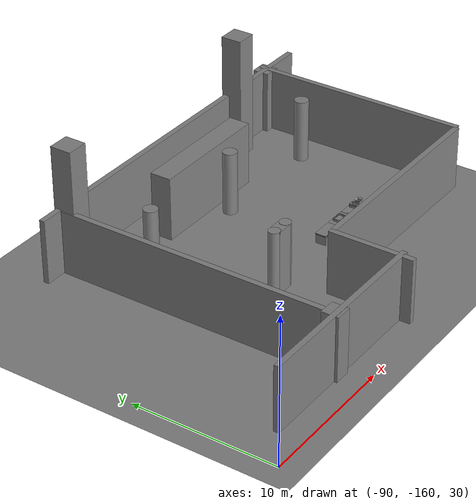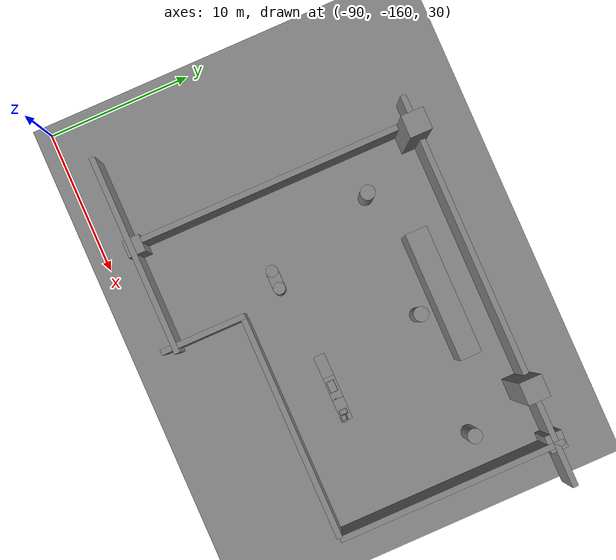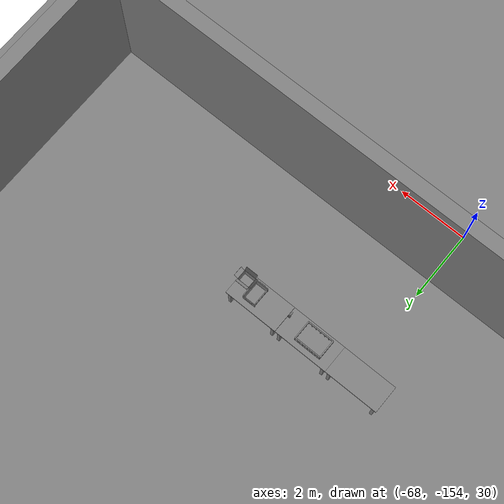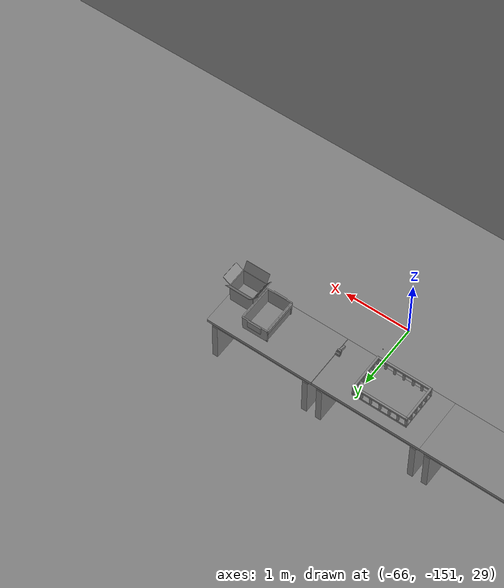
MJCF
<mujoco>
    <option gravity="0.000000000 0.000000000 -9.810000420" timestep="0.0049999999" integrator="implicitfast" density="1.225" viscosity="1.8000001e-05" noslip_iterations="10" iterations="100" sdf_iterations="50">
        <flag multiccd="disable"/>
    </option>
    <size memory="1000M"/>
    <compiler coordinate="local"/>
    <worldbody>
        <light cutoff="30" pos="0 1 1" dir="0 -1 -2"/>
        <light cutoff="30" pos="0 -1 1" dir="0 1 -2"/>
        <body pos="-64.866622925 -149.383972168 30.183746338" euler="89.999992371 89.999946594 0.000000000" name="openloong_gripper_2f85_fix_base_usda_bluebox_01">
            <geom contype="1" conaffinity="1" density="1000" type="box" material="" rgba="0.500000000 0.500000000 0.500000000 1.000000000" solimp="0.899999976 0.949999988 0.001000000" friction="1.000000000 0.005000000 0.000100000" solref="0.020000000 1.000000000" margin="0" condim="3" group="0" pos="0.276596069 0.187225342 0.000061035" quat="0.707107008 0.000077501 0.707106471 0.000077456" size="0.100000001 0.057999998 0.010000000" name="openloong_gripper_2f85_fix_base_usda_geom_140521B8_246C_4B0B_A355_C23E0F6084F3"/>
            <geom contype="1" conaffinity="1" density="1000" type="box" material="" rgba="0.500000000 0.500000000 0.500000000 1.000000000" solimp="0.899999976 0.949999988 0.001000000" friction="1.000000000 0.005000000 0.000100000" solref="0.020000000 1.000000000" margin="0" condim="3" group="0" pos="0.000000000 0.002883911 0.000000000" quat="1.000000000 0.000000000 0.000000000 0.000000000" size="0.254000008 0.003000000 0.172000006" name="openloong_gripper_2f85_fix_base_usda_geom_73622CF9_F985_40B0_9ED4_21AD3A3ABB41"/>
            <geom contype="1" conaffinity="1" density="1000" type="box" material="" rgba="0.500000000 0.500000000 0.500000000 1.000000000" solimp="0.899999976 0.949999988 0.001000000" friction="1.000000000 0.005000000 0.000100000" solref="0.020000000 1.000000000" margin="0" condim="3" group="0" pos="0.000015259 0.124874115 0.173477173" quat="0.999796450 0.020176515 -0.000000015 0.000000030" size="0.259999990 0.119999997 0.007000000" name="openloong_gripper_2f85_fix_base_usda_geom_8B6AA2DB_2FB7_4B84_B021_F9867B96E811"/>
            <geom contype="1" conaffinity="1" density="1000" type="box" material="" rgba="0.500000000 0.500000000 0.500000000 1.000000000" solimp="0.899999976 0.949999988 0.001000000" friction="1.000000000 0.005000000 0.000100000" solref="0.020000000 1.000000000" margin="0" condim="3" group="0" pos="0.000015259 0.124874115 -0.173477173" quat="0.999796450 -0.020176545 -0.000000015 0.000000000" size="0.259999990 0.119999997 0.007000000" name="openloong_gripper_2f85_fix_base_usda_geom_BA67179E_2182_4158_A999_9716A1910E65"/>
            <geom contype="1" conaffinity="1" density="1000" type="box" material="" rgba="0.500000000 0.500000000 0.500000000 1.000000000" solimp="0.899999976 0.949999988 0.001000000" friction="1.000000000 0.005000000 0.000100000" solref="0.020000000 1.000000000" margin="0" condim="3" group="0" pos="0.000015259 0.214012146 0.188980103" quat="0.999913096 0.013176724 0.000000015 0.000000000" size="0.259999990 0.029999999 0.012500000" name="openloong_gripper_2f85_fix_base_usda_geom_36C11384_9092_4C9A_92A4_36924CDBAB01"/>
            <geom contype="1" conaffinity="1" density="1000" type="box" material="" rgba="0.500000000 0.500000000 0.500000000 1.000000000" solimp="0.899999976 0.949999988 0.001000000" friction="1.000000000 0.005000000 0.000100000" solref="0.020000000 1.000000000" margin="0" condim="3" group="0" pos="-0.258346558 0.125289917 0.001876831" quat="0.702796996 -0.020792052 0.710783184 0.020769238" size="0.189999998 0.119999997 0.009000000" name="openloong_gripper_2f85_fix_base_usda_geom_B63E5D70_8A48_4B12_A339_93A92D8C35FE"/>
            <geom contype="1" conaffinity="1" density="1000" type="box" material="" rgba="0.500000000 0.500000000 0.500000000 1.000000000" solimp="0.899999976 0.949999988 0.001000000" friction="1.000000000 0.005000000 0.000100000" solref="0.020000000 1.000000000" margin="0" condim="3" group="0" pos="0.000015259 0.214012146 -0.188980103" quat="0.999913096 -0.013176769 0.000000030 0.000000015" size="0.259999990 0.029999999 0.012500000" name="openloong_gripper_2f85_fix_base_usda_geom_2EDD9D5D_4B59_4B01_821A_14A6AEE16678"/>
            <geom contype="1" conaffinity="1" density="1000" type="box" material="" rgba="0.500000000 0.500000000 0.500000000 1.000000000" solimp="0.899999976 0.949999988 0.001000000" friction="1.000000000 0.005000000 0.000100000" solref="0.020000000 1.000000000" margin="0" condim="3" group="0" pos="-0.276596069 0.187225342 0.000061035" quat="0.707106650 0.000077441 0.707106709 0.000077456" size="0.100000001 0.057999998 0.010000000" name="openloong_gripper_2f85_fix_base_usda_geom_71235923_C27E_4FD7_9AFA_B7AD034330A8"/>
            <geom contype="1" conaffinity="1" density="1000" type="box" material="" rgba="0.500000000 0.500000000 0.500000000 1.000000000" solimp="0.899999976 0.949999988 0.001000000" friction="1.000000000 0.005000000 0.000100000" solref="0.020000000 1.000000000" margin="0" condim="3" group="0" pos="0.258346558 0.125289917 0.001876831" quat="0.702851534 0.018856451 0.710823834 -0.019329429" size="0.189999998 0.119999997 0.009000000" name="openloong_gripper_2f85_fix_base_usda_geom_7BEA3804_6460_4FB0_849F_D74CC9CFBB47"/>
            <freejoint name="openloong_gripper_2f85_fix_base_usda_bluebox_01_joint"/>
            <site size="0.005000000 0.005000000 0.005000000" rgba="0.500000000 0.500000000 0.500000000 1.000000000" pos="0.000000000 0.000000000 0.000000000" quat="0.999961913 0.008726534 0.000000000 0.000000000" group="0" type="sphere" name="openloong_gripper_2f85_fix_base_usda_bluebox_01site"/>
        </body>
        <body pos="-64.496299744 -149.491867065 30.235729218" euler="0.000000000 0.000000000 89.999946594" name="openloong_gripper_2f85_fix_base_usda_cardboardbox_01">
            <geom contype="1" conaffinity="1" density="1000" type="box" material="" rgba="0.500000000 0.500000000 0.500000000 1.000000000" solimp="0.899999976 0.949999988 0.001000000" friction="1.000000000 0.005000000 0.000100000" solref="0.020000000 1.000000000" margin="0" condim="3" group="0" pos="-0.003166199 -0.004086494 0.005052090" quat="1.000000000 0.000000000 0.000000000 0.000000000" size="0.142499998 0.177500010 0.005000000" name="openloong_gripper_2f85_fix_base_usda_geom_E6B6A2F8_F4B2_4BDA_A704_061121B3D9BD"/>
            <geom contype="1" conaffinity="1" density="1000" type="box" material="" rgba="0.500000000 0.500000000 0.500000000 1.000000000" solimp="0.899999976 0.949999988 0.001000000" friction="1.000000000 0.005000000 0.000100000" solref="0.020000000 1.000000000" margin="0" condim="3" group="0" pos="-0.003166199 0.170316696 0.150570869" quat="1.000000000 0.000000000 0.000000000 0.000000000" size="0.142499998 0.005000000 0.149999991" name="openloong_gripper_2f85_fix_base_usda_geom_A12F14E5_720E_4E92_B818_8008D1F4811D"/>
            <geom contype="1" conaffinity="1" density="1000" type="box" material="" rgba="0.500000000 0.500000000 0.500000000 1.000000000" solimp="0.899999976 0.949999988 0.001000000" friction="1.000000000 0.005000000 0.000100000" solref="0.020000000 1.000000000" margin="0" condim="3" group="0" pos="-0.147399902 -0.005307198 0.150570869" quat="1.000000000 0.000000000 0.000000000 0.000000000" size="0.005000000 0.177500010 0.149999991" name="openloong_gripper_2f85_fix_base_usda_geom_9C82556C_F9BE_4016_92CE_BD5EC00E8E2F"/>
            <geom contype="1" conaffinity="1" density="1000" type="box" material="" rgba="0.500000000 0.500000000 0.500000000 1.000000000" solimp="0.899999976 0.949999988 0.001000000" friction="1.000000000 0.005000000 0.000100000" solref="0.020000000 1.000000000" margin="0" condim="3" group="0" pos="0.140275955 -0.005307198 0.150570869" quat="1.000000000 0.000000000 0.000000000 0.000000000" size="0.005000000 0.177500010 0.149999991" name="openloong_gripper_2f85_fix_base_usda_geom_AEE4A514_4011_4C65_B450_C55FE2598BB8"/>
            <geom contype="1" conaffinity="1" density="1000" type="box" material="" rgba="0.500000000 0.500000000 0.500000000 1.000000000" solimp="0.899999976 0.949999988 0.001000000" friction="1.000000000 0.005000000 0.000100000" solref="0.020000000 1.000000000" margin="0" condim="3" group="0" pos="-0.003166199 -0.181550980 0.150570869" quat="1.000000000 0.000000000 0.000000000 0.000000000" size="0.142499998 0.005000000 0.149999991" name="openloong_gripper_2f85_fix_base_usda_geom_5FAE7664_4644_4000_858E_9BEF79903E21"/>
            <freejoint name="openloong_gripper_2f85_fix_base_usda_cardboardbox_01_joint"/>
            <site size="0.005000000 0.005000000 0.005000000" rgba="0.500000000 0.500000000 0.500000000 1.000000000" pos="0.000000000 0.000000000 0.000000000" quat="0.999961913 0.008726535 0.000000000 0.000000000" group="0" type="sphere" name="openloong_gripper_2f85_fix_base_usda_site_F11E09BF_C0CC_42EB_B5E6_2E81762AA733"/>
            <body pos="0.139160156 -0.004048347 0.301930904" euler="-179.999954224 49.383502960 179.999954224" name="openloong_gripper_2f85_fix_base_usda_A1_006">
                <geom contype="1" conaffinity="1" density="1000" type="box" material="" rgba="0.500000000 0.500000000 0.500000000 1.000000000" solimp="0.899999976 0.949999988 0.001000000" friction="1.000000000 0.005000000 0.000100000" solref="0.020000000 1.000000000" margin="0" condim="3" group="0" pos="-0.071587563 0.000009537 0.001745224" quat="0.999999881 0.000000000 0.000000000 0.000000000" size="0.071249999 0.179999992 0.002500000" name="openloong_gripper_2f85_fix_base_usda_geom_68E40086_8973_4480_9921_5C87B88145A2"/>
                <joint armature="0" stiffness="0.07" damping="0.0099999998" axis="0.000000 1.000000 0.000000" type="hinge" name="openloong_gripper_2f85_fix_base_usda_A1_006"/>
            </body>
            <body pos="-0.145902634 -0.004086494 0.301938057" euler="-180.000000000 -60.000011444 -180.000000000" name="openloong_gripper_2f85_fix_base_usda_A2_006">
                <geom contype="1" conaffinity="1" density="1000" type="box" material="" rgba="0.500000000 0.500000000 0.500000000 1.000000000" solimp="0.899999976 0.949999988 0.001000000" friction="1.000000000 0.005000000 0.000100000" solref="0.020000000 1.000000000" margin="0" condim="3" group="0" pos="0.071268082 0.000009537 0.002717972" quat="0.000002921 0.000000000 -0.000000030 0.999999881" size="0.071249999 0.179999992 0.002500000" name="openloong_gripper_2f85_fix_base_usda_geom_69CD9053_F811_48E1_939C_E4CA980306C2"/>
                <joint armature="0" stiffness="0.07" damping="0.0099999998" axis="0.000000 1.000000 0.000000" type="hinge" name="openloong_gripper_2f85_fix_base_usda_A2_006"/>
            </body>
            <body pos="-0.003385544 0.175991058 0.301930904" euler="-125.858116150 -0.000004561 0.000002331" name="openloong_gripper_2f85_fix_base_usda_B2_006">
                <geom contype="1" conaffinity="1" density="1000" type="box" material="" rgba="0.500000000 0.500000000 0.500000000 1.000000000" solimp="0.899999976 0.949999988 0.001000000" friction="1.000000000 0.005000000 0.000100000" solref="0.020000000 1.000000000" margin="0" condim="3" group="0" pos="0.000009537 -0.070939064 -0.002470016" quat="0.999614120 0.027776197 -0.000000015 0.000000030" size="0.137500003 0.064999998 0.005000000" name="openloong_gripper_2f85_fix_base_usda_geom_3959AD9A_D23D_4FE3_A494_D8D4A26A73B4"/>
                <joint armature="0" stiffness="0.07" damping="0.0099999998" axis="1.000000 0.000000 0.000000" type="hinge" name="openloong_gripper_2f85_fix_base_usda_B2_006"/>
            </body>
            <body pos="-0.003385544 -0.184140205 0.301938057" euler="147.805557251 0.000000000 0.000000000" name="openloong_gripper_2f85_fix_base_usda_B1_006">
                <geom contype="1" conaffinity="1" density="1000" type="box" material="" rgba="0.500000000 0.500000000 0.500000000 1.000000000" solimp="0.899999976 0.949999988 0.001000000" friction="1.000000000 0.005000000 0.000100000" solref="0.020000000 1.000000000" margin="0" condim="3" group="0" pos="-0.000028610 0.070202351 -0.002703667" quat="0.999614179 -0.027776167 0.000000000 0.000000000" size="0.137500003 0.064999998 0.005000000" name="openloong_gripper_2f85_fix_base_usda_geom_87D76C0D_20C9_4EB2_8CC3_3DA2B9D9D119"/>
                <joint armature="0" stiffness="0.07" damping="0.0099999998" axis="1.000000 0.000000 0.000000" type="hinge" name="openloong_gripper_2f85_fix_base_usda_B1_006"/>
            </body>
        </body>
        <body pos="-65.882858276 -149.481979370 30.229999542" euler="-64.487716675 0.000000000 0.000000000" name="openloong_gripper_2f85_fix_base_usda_Barcode">
            <geom contype="1" conaffinity="1" density="1000" type="box" material="" rgba="0.500000000 0.500000000 0.500000000 1.000000000" solimp="0.899999976 0.949999988 0.001000000" friction="1.000000000 0.005000000 0.000100000" solref="0.020000000 1.000000000" margin="0" condim="3" group="0" pos="0.000000000 0.013038635 0.001419067" quat="0.000000000 0.000000000 0.000000000 1.000000119" size="0.034000002 0.010000000 0.017999999" name="openloong_gripper_2f85_fix_base_usda_geom_BD332ADF_A2EC_431A_9028_A1F37F06F7F2"/>
            <geom contype="1" conaffinity="1" density="1000" type="box" material="" rgba="0.500000000 0.500000000 0.500000000 1.000000000" solimp="0.899999976 0.949999988 0.001000000" friction="1.000000000 0.005000000 0.000100000" solref="0.020000000 1.000000000" margin="0" condim="3" group="0" pos="0.000000000 -0.035301208 -0.007095337" quat="0.000000000 0.000000000 -0.043619365 0.999048233" size="0.028999999 0.010000000 0.020000000" name="openloong_gripper_2f85_fix_base_usda_geom_0FA9DAEA_514A_4AB9_8F51_73DD916984E0"/>
            <geom contype="1" conaffinity="1" density="1000" type="box" material="" rgba="0.500000000 0.500000000 0.500000000 1.000000000" solimp="0.899999976 0.949999988 0.001000000" friction="1.000000000 0.005000000 0.000100000" solref="0.020000000 1.000000000" margin="0" condim="3" group="0" pos="0.000000000 -0.043411255 -0.011749268" quat="0.922262907 0.386563420 0.000000000 0.000000000" size="0.026000001 0.010000000 0.020000000" name="openloong_gripper_2f85_fix_base_usda_geom_7A949876_5F9D_427A_AA58_69331B2E1468"/>
            <geom contype="1" conaffinity="1" density="1000" type="box" material="" rgba="0.500000000 0.500000000 0.500000000 1.000000000" solimp="0.899999976 0.949999988 0.001000000" friction="1.000000000 0.005000000 0.000100000" solref="0.020000000 1.000000000" margin="0" condim="3" group="0" pos="0.000000000 -0.016967773 -0.031860352" quat="0.000000000 0.000000000 0.000000000 1.000000119" size="0.008000000 0.010000000 0.013000000" name="openloong_gripper_2f85_fix_base_usda_geom_5CE1C300_2549_4B96_8C2F_3C0D44AEF483"/>
            <geom contype="1" conaffinity="1" density="1000" type="box" material="" rgba="0.500000000 0.500000000 0.500000000 1.000000000" solimp="0.899999976 0.949999988 0.001000000" friction="1.000000000 0.005000000 0.000100000" solref="0.020000000 1.000000000" margin="0" condim="3" group="0" pos="0.000000000 -0.001869202 0.000312805" quat="0.953716993 0.300705761 0.000000000 0.000000000" size="0.032000002 0.010000000 0.018999999" name="openloong_gripper_2f85_fix_base_usda_geom_4B64C8DD_9125_425A_8FFF_E11A331548FD"/>
            <geom contype="1" conaffinity="1" density="1000" type="box" material="" rgba="0.500000000 0.500000000 0.500000000 1.000000000" solimp="0.899999976 0.949999988 0.001000000" friction="1.000000000 0.005000000 0.000100000" solref="0.020000000 1.000000000" margin="0" condim="3" group="0" pos="0.000000000 -0.019531250 -0.003173828" quat="0.953716993 0.300705761 0.000000000 0.000000000" size="0.030999999 0.010000000 0.020000000" name="openloong_gripper_2f85_fix_base_usda_geom_EBE6E8D6_8133_4E0D_BE00_0D804527B1C8"/>
            <geom contype="1" conaffinity="1" density="1000" type="box" material="" rgba="0.500000000 0.500000000 0.500000000 1.000000000" solimp="0.899999976 0.949999988 0.001000000" friction="1.000000000 0.005000000 0.000100000" solref="0.020000000 1.000000000" margin="0" condim="3" group="0" pos="0.000000000 -0.035301208 -0.007095337" quat="0.953716993 0.300705761 0.000000000 0.000000000" size="0.028999999 0.010000000 0.020000000" name="openloong_gripper_2f85_fix_base_usda_geom_72BBB484_ABD0_47D6_B9BF_B9A9D410FB58"/>
            <geom contype="1" conaffinity="1" density="1000" type="box" material="" rgba="0.500000000 0.500000000 0.500000000 1.000000000" solimp="0.899999976 0.949999988 0.001000000" friction="1.000000000 0.005000000 0.000100000" solref="0.020000000 1.000000000" margin="0" condim="3" group="0" pos="0.000000000 -0.042617798 -0.071121216" quat="0.000000000 0.000000000 0.000000000 1.000000119" size="0.013000000 0.021000000 0.059999999" name="openloong_gripper_2f85_fix_base_usda_geom_9E0C6AE4_DF0B_42A4_A034_04E811D4062B"/>
            <freejoint name="openloong_gripper_2f85_fix_base_usda_Barcode_joint"/>
            <site size="0.005000000 0.005000000 0.005000000" rgba="0.500000000 0.500000000 0.500000000 1.000000000" pos="0.000000000 0.000000000 0.000000000" quat="1.000000000 0.000000000 0.000000000 0.000000000" group="0" type="sphere" name="openloong_gripper_2f85_fix_base_usda_Barcode_site"/>
        </body>
        <body pos="-66.745018005 -149.392349243 30.184000015" euler="0.000000000 0.000000000 89.999946594" name="[22331120194300]_Basket_01">
            <geom contype="1" conaffinity="1" density="1000" type="box" material="" rgba="0.500000000 0.500000000 0.500000000 1.000000000" solimp="0.899999976 0.949999988 0.001000000" friction="1.000000000 0.005000000 0.000100000" solref="0.020000000 1.000000000" margin="0" condim="3" group="0" pos="-0.052425385 0.389207840 0.089787483" quat="0.707107008 0.000000000 0.000000000 0.707106411" size="0.014249999 0.014249999 0.059999999" name="[22331120194300]_geom_10D7C19F_AA76_4DD0_87AB_7185B409F535"/>
            <geom contype="1" conaffinity="1" density="1000" type="box" material="" rgba="0.500000000 0.500000000 0.500000000 1.000000000" solimp="0.899999976 0.949999988 0.001000000" friction="1.000000000 0.005000000 0.000100000" solref="0.020000000 1.000000000" margin="0" condim="3" group="0" pos="0.264015198 -0.133043289 0.089787483" quat="0.707107008 0.000000000 0.000000000 0.707106411" size="0.014249999 0.014249999 0.059999999" name="[22331120194300]_geom_7784EB04_97EB_469A_AE3F_E26E2E3214FE"/>
            <geom contype="1" conaffinity="1" density="1000" type="box" material="" rgba="0.500000000 0.500000000 0.500000000 1.000000000" solimp="0.899999976 0.949999988 0.001000000" friction="1.000000000 0.005000000 0.000100000" solref="0.020000000 1.000000000" margin="0" condim="3" group="0" pos="-0.264015198 -0.265548706 0.089793205" quat="0.707107008 0.000000000 0.000000000 0.707106411" size="0.014249999 0.014249999 0.059999999" name="[22331120194300]_geom_96142D1E_B73A_4220_A0AD_AF8BEBF4278F"/>
            <geom contype="1" conaffinity="1" density="1000" type="box" material="" rgba="0.500000000 0.500000000 0.500000000 1.000000000" solimp="0.899999976 0.949999988 0.001000000" friction="1.000000000 0.005000000 0.000100000" solref="0.020000000 1.000000000" margin="0" condim="3" group="0" pos="-0.160263062 -0.389322281 0.089793205" quat="0.707107008 0.000000000 0.000000000 0.707106411" size="0.014249999 0.014249999 0.059999999" name="[22331120194300]_geom_4C88BBC6_6E9F_4FBA_9FBB_1FA3461EA0E1"/>
            <geom contype="1" conaffinity="1" density="1000" type="box" material="" rgba="0.500000000 0.500000000 0.500000000 1.000000000" solimp="0.899999976 0.949999988 0.001000000" friction="1.000000000 0.005000000 0.000100000" solref="0.020000000 1.000000000" margin="0" condim="3" group="0" pos="0.162265778 -0.389322281 0.089787483" quat="0.707107008 0.000000000 0.000000000 0.707106411" size="0.014249999 0.014249999 0.059999999" name="[22331120194300]_geom_AFE16ACC_6EB1_47AA_A964_C70771665647"/>
            <geom contype="1" conaffinity="1" density="1000" type="box" material="" rgba="0.500000000 0.500000000 0.500000000 1.000000000" solimp="0.899999976 0.949999988 0.001000000" friction="1.000000000 0.005000000 0.000100000" solref="0.020000000 1.000000000" margin="0" condim="3" group="0" pos="0.264015198 0.389207840 0.089787483" quat="0.707107008 0.000000000 0.000000000 0.707106411" size="0.014249999 0.014249999 0.059999999" name="[22331120194300]_geom_AF046882_4D70_4AD5_ABF6_D54869F4B6AE"/>
            <geom contype="1" conaffinity="1" density="1000" type="box" material="" rgba="0.500000000 0.500000000 0.500000000 1.000000000" solimp="0.899999976 0.949999988 0.001000000" friction="1.000000000 0.005000000 0.000100000" solref="0.020000000 1.000000000" margin="0" condim="3" group="0" pos="-0.264015198 -0.133043289 0.089793205" quat="0.707107008 0.000000000 0.000000000 0.707106411" size="0.014249999 0.014249999 0.059999999" name="[22331120194300]_geom_ABEEF05A_52C8_462B_81F2_F4631F19AB8C"/>
            <geom contype="1" conaffinity="1" density="1000" type="box" material="" rgba="0.500000000 0.500000000 0.500000000 1.000000000" solimp="0.899999976 0.949999988 0.001000000" friction="1.000000000 0.005000000 0.000100000" solref="0.020000000 1.000000000" margin="0" condim="3" group="0" pos="-0.264026642 0.269256592 0.089793205" quat="0.707107008 0.000000000 0.000000000 0.707106411" size="0.014249999 0.014249999 0.059999999" name="[22331120194300]_geom_2BA3B31A_A5D6_49A9_9A49_DDC329A191C4"/>
            <geom contype="1" conaffinity="1" density="1000" type="box" material="" rgba="0.500000000 0.500000000 0.500000000 1.000000000" solimp="0.899999976 0.949999988 0.001000000" friction="1.000000000 0.005000000 0.000100000" solref="0.020000000 1.000000000" margin="0" condim="3" group="0" pos="0.054462433 0.389207840 0.089787483" quat="0.707107008 0.000000000 0.000000000 0.707106411" size="0.014249999 0.014249999 0.059999999" name="[22331120194300]_geom_8BC939CC_1A61_4FCB_B617_22DE5798621C"/>
            <geom contype="1" conaffinity="1" density="1000" type="box" material="" rgba="0.500000000 0.500000000 0.500000000 1.000000000" solimp="0.899999976 0.949999988 0.001000000" friction="1.000000000 0.005000000 0.000100000" solref="0.020000000 1.000000000" margin="0" condim="3" group="0" pos="0.054462433 -0.389322281 0.089787483" quat="0.707107008 0.000000000 0.000000000 0.707106411" size="0.014249999 0.014249999 0.059999999" name="[22331120194300]_geom_8F92A3A8_62CD_4F12_B0F5_78A1021B3B05"/>
            <geom contype="1" conaffinity="1" density="1000" type="box" material="" rgba="0.500000000 0.500000000 0.500000000 1.000000000" solimp="0.899999976 0.949999988 0.001000000" friction="1.000000000 0.005000000 0.000100000" solref="0.020000000 1.000000000" margin="0" condim="3" group="0" pos="0.264015198 0.269256592 0.089793205" quat="0.707107008 0.000000000 0.000000000 0.707106411" size="0.014249999 0.014249999 0.059999999" name="[22331120194300]_geom_546ECE9E_4280_4288_9E0B_EB7419714167"/>
            <geom contype="1" conaffinity="1" density="1000" type="box" material="" rgba="0.500000000 0.500000000 0.500000000 1.000000000" solimp="0.899999976 0.949999988 0.001000000" friction="1.000000000 0.005000000 0.000100000" solref="0.020000000 1.000000000" margin="0" condim="3" group="0" pos="0.264015198 -0.389322281 0.089787483" quat="0.707107008 0.000000000 0.000000000 0.707106411" size="0.014249999 0.014249999 0.059999999" name="[22331120194300]_geom_52BECAE7_7FE2_4459_A3F9_E6189CC53EBA"/>
            <geom contype="1" conaffinity="1" density="1000" type="box" material="" rgba="0.500000000 0.500000000 0.500000000 1.000000000" solimp="0.899999976 0.949999988 0.001000000" friction="1.000000000 0.005000000 0.000100000" solref="0.020000000 1.000000000" margin="0" condim="3" group="0" pos="0.000000000 0.000000000 0.015998840" quat="0.707107008 0.000000000 0.000000000 0.707106411" size="0.403499991 0.279000014 0.015750000" name="[22331120194300]_geom_70516354_D210_49CC_BEE6_CA001FB14BE6"/>
            <geom contype="1" conaffinity="1" density="1000" type="box" material="" rgba="0.500000000 0.500000000 0.500000000 1.000000000" solimp="0.899999976 0.949999988 0.001000000" friction="1.000000000 0.005000000 0.000100000" solref="0.020000000 1.000000000" margin="0" condim="3" group="0" pos="0.000000000 -0.389476776 0.163619041" quat="0.707107008 0.000000000 0.000000000 0.707106411" size="0.015000000 0.277500004 0.015750000" name="[22331120194300]_geom_478B59C6_85E8_448E_916F_DB713985FCC7"/>
            <geom contype="1" conaffinity="1" density="1000" type="box" material="" rgba="0.500000000 0.500000000 0.500000000 1.000000000" solimp="0.899999976 0.949999988 0.001000000" friction="1.000000000 0.005000000 0.000100000" solref="0.020000000 1.000000000" margin="0" condim="3" group="0" pos="0.162265778 0.389207840 0.089787483" quat="0.707107008 0.000000000 0.000000000 0.707106411" size="0.014249999 0.014249999 0.059999999" name="[22331120194300]_geom_4310FF4E_7B67_401C_A6D4_0A07B96B1605"/>
            <geom contype="1" conaffinity="1" density="1000" type="box" material="" rgba="0.500000000 0.500000000 0.500000000 1.000000000" solimp="0.899999976 0.949999988 0.001000000" friction="1.000000000 0.005000000 0.000100000" solref="0.020000000 1.000000000" margin="0" condim="3" group="0" pos="0.000000000 0.389471054 0.163619041" quat="0.707107008 0.000000000 0.000000000 0.707106411" size="0.015000000 0.277500004 0.015750000" name="[22331120194300]_geom_0839A856_9C87_4FDF_BA7A_0E11A8A37D6D"/>
            <geom contype="1" conaffinity="1" density="1000" type="box" material="" rgba="0.500000000 0.500000000 0.500000000 1.000000000" solimp="0.899999976 0.949999988 0.001000000" friction="1.000000000 0.005000000 0.000100000" solref="0.020000000 1.000000000" margin="0" condim="3" group="0" pos="-0.263511658 0.000000000 0.163619041" quat="0.707107008 0.000000000 0.000000000 0.707106411" size="0.403499991 0.015000000 0.015750000" name="[22331120194300]_geom_AD0E0258_553D_42A3_8C36_FAEDF259B097"/>
            <geom contype="1" conaffinity="1" density="1000" type="box" material="" rgba="0.500000000 0.500000000 0.500000000 1.000000000" solimp="0.899999976 0.949999988 0.001000000" friction="1.000000000 0.005000000 0.000100000" solref="0.020000000 1.000000000" margin="0" condim="3" group="0" pos="-0.264015198 0.141334534 0.089793205" quat="0.707107008 0.000000000 0.000000000 0.707106411" size="0.014249999 0.014249999 0.059999999" name="[22331120194300]_geom_D4603B62_87C4_4A98_B0C3_832DDAE4F532"/>
            <geom contype="1" conaffinity="1" density="1000" type="box" material="" rgba="0.500000000 0.500000000 0.500000000 1.000000000" solimp="0.899999976 0.949999988 0.001000000" friction="1.000000000 0.005000000 0.000100000" solref="0.020000000 1.000000000" margin="0" condim="3" group="0" pos="0.264015198 -0.265548706 0.089787483" quat="0.707107008 0.000000000 0.000000000 0.707106411" size="0.014249999 0.014249999 0.059999999" name="[22331120194300]_geom_9CC63A2C_D57E_46E9_97DD_EBA08084E0EB"/>
            <geom contype="1" conaffinity="1" density="1000" type="box" material="" rgba="0.500000000 0.500000000 0.500000000 1.000000000" solimp="0.899999976 0.949999988 0.001000000" friction="1.000000000 0.005000000 0.000100000" solref="0.020000000 1.000000000" margin="0" condim="3" group="0" pos="-0.160263062 0.389207840 0.089787483" quat="0.707107008 0.000000000 0.000000000 0.707106411" size="0.014249999 0.014249999 0.059999999" name="[22331120194300]_geom_84A1E925_2FFA_4E5D_B4FB_5A68BA13E66A"/>
            <geom contype="1" conaffinity="1" density="1000" type="box" material="" rgba="0.500000000 0.500000000 0.500000000 1.000000000" solimp="0.899999976 0.949999988 0.001000000" friction="1.000000000 0.005000000 0.000100000" solref="0.020000000 1.000000000" margin="0" condim="3" group="0" pos="-0.052425385 -0.389322281 0.089787483" quat="0.707107008 0.000000000 0.000000000 0.707106411" size="0.014249999 0.014249999 0.059999999" name="[22331120194300]_geom_8CAD8DD4_9FC1_479E_B42E_25E87CD7F388"/>
            <geom contype="1" conaffinity="1" density="1000" type="box" material="" rgba="0.500000000 0.500000000 0.500000000 1.000000000" solimp="0.899999976 0.949999988 0.001000000" friction="1.000000000 0.005000000 0.000100000" solref="0.020000000 1.000000000" margin="0" condim="3" group="0" pos="-0.264026642 -0.389322281 0.089793205" quat="0.707107008 0.000000000 0.000000000 0.707106411" size="0.014249999 0.014249999 0.059999999" name="[22331120194300]_geom_8D9F88A1_B0FA_4FEB_8FEB_0E2D8274E6B7"/>
            <geom contype="1" conaffinity="1" density="1000" type="box" material="" rgba="0.500000000 0.500000000 0.500000000 1.000000000" solimp="0.899999976 0.949999988 0.001000000" friction="1.000000000 0.005000000 0.000100000" solref="0.020000000 1.000000000" margin="0" condim="3" group="0" pos="0.264015198 0.141334534 0.089787483" quat="0.707107008 0.000000000 0.000000000 0.707106411" size="0.014249999 0.014249999 0.059999999" name="[22331120194300]_geom_81FF58C7_5CFC_4761_9E4F_94AF0076F386"/>
            <geom contype="1" conaffinity="1" density="1000" type="box" material="" rgba="0.500000000 0.500000000 0.500000000 1.000000000" solimp="0.899999976 0.949999988 0.001000000" friction="1.000000000 0.005000000 0.000100000" solref="0.020000000 1.000000000" margin="0" condim="3" group="0" pos="-0.264015198 0.389207840 0.089793205" quat="0.707107008 0.000000000 0.000000000 0.707106411" size="0.014249999 0.014249999 0.059999999" name="[22331120194300]_geom_99997E1A_A13E_471E_84B2_9BA98ACDDB21"/>
            <geom contype="1" conaffinity="1" density="1000" type="box" material="" rgba="0.500000000 0.500000000 0.500000000 1.000000000" solimp="0.899999976 0.949999988 0.001000000" friction="1.000000000 0.005000000 0.000100000" solref="0.020000000 1.000000000" margin="0" condim="3" group="0" pos="0.264015198 0.004480362 0.089787483" quat="0.707107008 0.000000000 0.000000000 0.707106411" size="0.014249999 0.014249999 0.059999999" name="[22331120194300]_geom_334E54D4_060E_4FA3_9EF6_950C92289DF8"/>
            <geom contype="1" conaffinity="1" density="1000" type="box" material="" rgba="0.500000000 0.500000000 0.500000000 1.000000000" solimp="0.899999976 0.949999988 0.001000000" friction="1.000000000 0.005000000 0.000100000" solref="0.020000000 1.000000000" margin="0" condim="3" group="0" pos="0.263694763 -0.000011444 0.163619041" quat="0.707107008 0.000000000 0.000000000 0.707106411" size="0.403499991 0.015000000 0.015750000" name="[22331120194300]_geom_A2FF47C4_B948_431F_8767_059B380E8317"/>
            <geom contype="1" conaffinity="1" density="1000" type="box" material="" rgba="0.500000000 0.500000000 0.500000000 1.000000000" solimp="0.899999976 0.949999988 0.001000000" friction="1.000000000 0.005000000 0.000100000" solref="0.020000000 1.000000000" margin="0" condim="3" group="0" pos="-0.264015198 0.004480362 0.089793205" quat="0.707107008 0.000000000 0.000000000 0.707106411" size="0.014249999 0.014249999 0.059999999" name="[22331120194300]_geom_45C91E7A_3B1B_4496_8D8A_3468E201016D"/>
            <freejoint name="[22331120194300]_joint_948DDCD8_990C_441A_B9D3_34F4D14B6D1C"/>
        </body>
        <body pos="0.000000000 0.000000000 0.000000000" euler="0.000000000 0.000000000 0.000000000" name="Static Objects_Static Objects">
            <geom contype="1" conaffinity="1" density="1000" type="box" material="" rgba="0.500000000 0.500000000 0.500000000 1.000000000" solimp="0.899999976 0.949999988 0.001000000" friction="1.000000000 0.005000000 0.000100000" solref="0.020000000 1.000000000" margin="0" condim="3" group="0" pos="-67.544113159 -149.365814209 29.727830887" quat="0.500000417 0.499999970 0.499999553 0.499999970" size="0.381000012 0.319999993 0.041000001" name="Static Objects_geom_9D5CA45D_B8BF_4BA6_AD94_F812C0AB5F09"/>
            <geom contype="1" conaffinity="1" density="1000" type="box" material="" rgba="0.500000000 0.500000000 0.500000000 1.000000000" solimp="0.899999976 0.949999988 0.001000000" friction="1.000000000 0.005000000 0.000100000" solref="0.020000000 1.000000000" margin="0" condim="3" group="0" pos="-68.239501953 -149.365814209 30.086868286" quat="0.500000417 0.499999970 0.499999553 0.499999970" size="0.370999992 0.039500002 0.745000005" name="Static Objects_geom_58A26DCA_CAE9_4D13_9784_BF1AC96A8532"/>
            <geom contype="1" conaffinity="1" density="1000" type="box" material="" rgba="0.500000000 0.500000000 0.500000000 1.000000000" solimp="0.899999976 0.949999988 0.001000000" friction="1.000000000 0.005000000 0.000100000" solref="0.020000000 1.000000000" margin="0" condim="3" group="0" pos="-68.239501953 -149.365814209 30.147235870" quat="0.500000417 0.499999970 0.499999553 0.499999970" size="0.400000006 0.022000000 0.800000012" name="Static Objects_geom_45FA5CFE_2C7F_4ACA_9DF2_DB0D904AAEE2"/>
            <geom contype="1" conaffinity="1" density="1000" type="box" material="" rgba="0.500000000 0.500000000 0.500000000 1.000000000" solimp="0.899999976 0.949999988 0.001000000" friction="1.000000000 0.005000000 0.000100000" solref="0.020000000 1.000000000" margin="0" condim="3" group="0" pos="-68.934890747 -149.365814209 29.727830887" quat="0.500000417 0.499999970 0.499999553 0.499999970" size="0.381000012 0.319999993 0.041000001" name="Static Objects_geom_C69986FA_05CD_43DC_A408_CFFA7F9FBC48"/>
            <geom contype="1" conaffinity="1" density="1000" type="box" material="" rgba="0.500000000 0.500000000 0.500000000 1.000000000" solimp="0.899999976 0.949999988 0.001000000" friction="1.000000000 0.005000000 0.000100000" solref="0.020000000 1.000000000" margin="0" condim="3" group="0" pos="-68.239501953 -149.365814209 29.561563492" quat="0.500000417 0.499999970 0.499999553 0.499999970" size="0.020000000 0.022000000 0.660000026" name="Static Objects_geom_04B8F39E_A401_495F_B4D6_A0E2BBBB32E8"/>
            <geom contype="1" conaffinity="1" density="1000" type="box" material="" rgba="0.500000000 0.500000000 0.500000000 1.000000000" solimp="0.899999976 0.949999988 0.001000000" friction="1.000000000 0.005000000 0.000100000" solref="0.020000000 1.000000000" margin="0" condim="3" group="0" pos="-65.945671082 -149.365814209 29.727830887" quat="0.500000417 0.499999970 0.499999553 0.499999970" size="0.381000012 0.319999993 0.041000001" name="Static Objects_geom_59F956CE_C010_4FF7_A64B_7F55DB7AF616"/>
            <geom contype="1" conaffinity="1" density="1000" type="box" material="" rgba="0.500000000 0.500000000 0.500000000 1.000000000" solimp="0.899999976 0.949999988 0.001000000" friction="1.000000000 0.005000000 0.000100000" solref="0.020000000 1.000000000" margin="0" condim="3" group="0" pos="-66.641059875 -149.365814209 30.086868286" quat="0.500000417 0.499999970 0.499999553 0.499999970" size="0.370999992 0.039500002 0.745000005" name="Static Objects_geom_7D3DADA5_00E3_41AC_8C88_327941FAAEBD"/>
            <geom contype="1" conaffinity="1" density="1000" type="box" material="" rgba="0.500000000 0.500000000 0.500000000 1.000000000" solimp="0.899999976 0.949999988 0.001000000" friction="1.000000000 0.005000000 0.000100000" solref="0.020000000 1.000000000" margin="0" condim="3" group="0" pos="-66.641059875 -149.365814209 30.147235870" quat="0.500000417 0.499999970 0.499999553 0.499999970" size="0.400000006 0.022000000 0.800000012" name="Static Objects_geom_46ABB7BC_7539_4506_857C_316E4CA26E4A"/>
            <geom contype="1" conaffinity="1" density="1000" type="box" material="" rgba="0.500000000 0.500000000 0.500000000 1.000000000" solimp="0.899999976 0.949999988 0.001000000" friction="1.000000000 0.005000000 0.000100000" solref="0.020000000 1.000000000" margin="0" condim="3" group="0" pos="-67.336448669 -149.365814209 29.727830887" quat="0.500000417 0.499999970 0.499999553 0.499999970" size="0.381000012 0.319999993 0.041000001" name="Static Objects_geom_CF13DE38_4747_4E98_A1C4_DE8EBF84DF2F"/>
            <geom contype="1" conaffinity="1" density="1000" type="box" material="" rgba="0.500000000 0.500000000 0.500000000 1.000000000" solimp="0.899999976 0.949999988 0.001000000" friction="1.000000000 0.005000000 0.000100000" solref="0.020000000 1.000000000" margin="0" condim="3" group="0" pos="-66.641059875 -149.365814209 29.561563492" quat="0.500000417 0.499999970 0.499999553 0.499999970" size="0.020000000 0.022000000 0.660000026" name="Static Objects_geom_BBB2255F_318F_4AB8_A269_FD21EA8275F7"/>
            <geom contype="1" conaffinity="1" density="1000" type="box" material="" rgba="0.500000000 0.500000000 0.500000000 1.000000000" solimp="0.899999976 0.949999988 0.001000000" friction="1.000000000 0.005000000 0.000100000" solref="0.020000000 1.000000000" margin="0" condim="3" group="0" pos="-64.338577271 -149.365814209 29.727830887" quat="0.500000417 0.499999970 0.499999553 0.499999970" size="0.381000012 0.319999993 0.041000001" name="Static Objects_geom_11E2A25F_D53E_480A_9AA8_793213D37EA3"/>
            <geom contype="1" conaffinity="1" density="1000" type="box" material="" rgba="0.500000000 0.500000000 0.500000000 1.000000000" solimp="0.899999976 0.949999988 0.001000000" friction="1.000000000 0.005000000 0.000100000" solref="0.020000000 1.000000000" margin="0" condim="3" group="0" pos="-65.033966064 -149.365814209 30.086868286" quat="0.500000417 0.499999970 0.499999553 0.499999970" size="0.370999992 0.039500002 0.745000005" name="Static Objects_geom_7E886058_77BB_40FA_AC03_E32E45776107"/>
            <geom contype="1" conaffinity="1" density="1000" type="box" material="" rgba="0.500000000 0.500000000 0.500000000 1.000000000" solimp="0.899999976 0.949999988 0.001000000" friction="1.000000000 0.005000000 0.000100000" solref="0.020000000 1.000000000" margin="0" condim="3" group="0" pos="-65.033966064 -149.365814209 30.147235870" quat="0.500000417 0.499999970 0.499999553 0.499999970" size="0.400000006 0.022000000 0.800000012" name="Static Objects_geom_E3A38CFF_EEC7_44C3_9BD2_F905EE1BB43D"/>
            <geom contype="1" conaffinity="1" density="1000" type="box" material="" rgba="0.500000000 0.500000000 0.500000000 1.000000000" solimp="0.899999976 0.949999988 0.001000000" friction="1.000000000 0.005000000 0.000100000" solref="0.020000000 1.000000000" margin="0" condim="3" group="0" pos="-65.729354858 -149.365814209 29.727830887" quat="0.500000417 0.499999970 0.499999553 0.499999970" size="0.381000012 0.319999993 0.041000001" name="Static Objects_geom_822DD4F5_0D7C_4626_9409_BB4C290E597A"/>
            <geom contype="1" conaffinity="1" density="1000" type="box" material="" rgba="0.500000000 0.500000000 0.500000000 1.000000000" solimp="0.899999976 0.949999988 0.001000000" friction="1.000000000 0.005000000 0.000100000" solref="0.020000000 1.000000000" margin="0" condim="3" group="0" pos="-65.033966064 -149.365814209 29.561563492" quat="0.500000417 0.499999970 0.499999553 0.499999970" size="0.020000000 0.022000000 0.660000026" name="Static Objects_geom_C932D327_746F_4E95_8299_9E291B3E5DD3"/>
            <geom contype="1" conaffinity="1" density="1000" type="box" material="" rgba="0.500000000 0.500000000 0.500000000 1.000000000" solimp="0.899999976 0.949999988 0.001000000" friction="1.000000000 0.005000000 0.000100000" solref="0.020000000 1.000000000" margin="0" condim="3" group="0" pos="-61.754566193 -137.853729248 33.906845093" quat="0.707107067 0.000000000 0.000000000 0.707106471" size="0.759999990 0.759999990 4.500000000" name="Static Objects_geom_D9BC61EF_1E2A_4EE2_A6D2_F44DE679579D"/>
            <geom contype="1" conaffinity="1" density="1000" type="box" material="" rgba="0.500000000 0.500000000 0.500000000 1.000000000" solimp="0.899999976 0.949999988 0.001000000" friction="1.000000000 0.005000000 0.000100000" solref="0.020000000 1.000000000" margin="0" condim="3" group="0" pos="-57.511135101 -144.927108765 31.707921982" quat="1.000000000 0.000000000 0.000000000 0.000000000" size="0.200000003 8.000000000 2.299999952" name="Static Objects_geom_EA48D8E8_CCEE_46AC_BC51_9FEDC93FD0AF"/>
            <geom contype="1" conaffinity="1" density="1000" type="box" material="" rgba="0.500000000 0.500000000 0.500000000 1.000000000" solimp="0.899999976 0.949999988 0.001000000" friction="1.000000000 0.005000000 0.000100000" solref="0.020000000 1.000000000" margin="0" condim="3" group="0" pos="-80.517646790 -157.574050903 31.688196182" quat="0.707107067 0.000000000 0.000000000 0.707106471" size="0.600000024 0.600000024 2.299999952" name="Static Objects_geom_2AC51885_7A80_4CE9_8E13_F2E0E10521C8"/>
            <geom contype="1" conaffinity="1" density="1000" type="box" material="" rgba="0.500000000 0.500000000 0.500000000 1.000000000" solimp="0.899999976 0.949999988 0.001000000" friction="1.000000000 0.005000000 0.000100000" solref="0.020000000 1.000000000" margin="0" condim="3" group="0" pos="-80.711044312 -147.414932251 31.666158676" quat="1.000000000 0.000000000 0.000000000 0.000000000" size="0.200000003 10.000000000 2.299999952" name="Static Objects_geom_B198D441_0AF5_49D2_89FA_469FCD786AE0"/>
            <geom contype="1" conaffinity="1" density="1000" type="box" material="" rgba="0.500000000 0.500000000 0.500000000 1.000000000" solimp="0.899999976 0.949999988 0.001000000" friction="1.000000000 0.005000000 0.000100000" solref="0.020000000 1.000000000" margin="0" condim="3" group="0" pos="-57.687217712 -137.434692383 31.688196182" quat="0.707107067 0.000000000 0.000000000 0.707106471" size="0.600000024 0.600000024 2.299999952" name="Static Objects_geom_7E017BCD_77C4_4D3F_8794_C3FF3200972A"/>
            <geom contype="1" conaffinity="1" density="1000" type="box" material="" rgba="0.500000000 0.500000000 0.500000000 1.000000000" solimp="0.899999976 0.949999988 0.001000000" friction="1.000000000 0.005000000 0.000100000" solref="0.020000000 1.000000000" margin="0" condim="3" group="0" pos="-69.537033081 -140.263229370 31.714921951" quat="0.707107067 0.000000000 0.000000000 0.707106471" size="0.759999990 4.500000000 2.299999952" name="Static Objects_geom_FFF34749_2182_45E6_A31D_B435C57A2974"/>
            <geom contype="1" conaffinity="1" density="1000" type="box" material="" rgba="0.500000000 0.500000000 0.500000000 1.000000000" solimp="0.899999976 0.949999988 0.001000000" friction="1.000000000 0.005000000 0.000100000" solref="0.020000000 1.000000000" margin="0" condim="3" group="0" pos="-80.073638916 -137.853713989 33.906845093" quat="0.707107067 0.000000000 0.000000000 0.707106471" size="0.759999990 0.759999990 4.500000000" name="Static Objects_geom_8AB31191_34D5_4B84_ABA9_4C3465F05038"/>
            <geom contype="1" conaffinity="1" density="1000" type="box" material="" rgba="0.500000000 0.500000000 0.500000000 1.000000000" solimp="0.899999976 0.949999988 0.001000000" friction="1.000000000 0.005000000 0.000100000" solref="0.020000000 1.000000000" margin="0" condim="3" group="0" pos="-73.406707764 -155.734664917 31.707921982" quat="1.000000000 0.000000000 0.000000000 0.000000000" size="0.200000003 3.000000000 2.299999952" name="Static Objects_geom_9CFB1A2F_BD64_4AE9_BCF6_EF89949615B9"/>
            <geom contype="1" conaffinity="1" density="1000" type="box" material="" rgba="0.500000000 0.500000000 0.500000000 1.000000000" solimp="0.899999976 0.949999988 0.001000000" friction="1.000000000 0.005000000 0.000100000" solref="0.020000000 1.000000000" margin="0" condim="3" group="0" pos="-68.497543335 -137.448257446 31.707921982" quat="0.707107067 0.000000000 0.000000000 0.707106471" size="0.200000003 14.000000000 2.299999952" name="Static Objects_geom_C489DCDB_1985_4481_8A95_3F5288E0B7DF"/>
            <geom contype="1" conaffinity="1" density="1000" type="cylinder" material="" rgba="0.500000000 0.500000000 0.500000000 1.000000000" solimp="0.899999976 0.949999988 0.001000000" friction="1.000000000 0.005000000 0.000100000" solref="0.020000000 1.000000000" margin="0" condim="3" group="0" pos="-68.868522644 -142.134506226 31.711090088" quat="0.707107067 0.000000000 0.000000000 0.707106471" size="0.509999990 2.299999952 1.000000000" name="Static Objects_geom_EF44D53A_1582_45C0_8C27_1886D1E1EB53"/>
            <geom contype="1" conaffinity="1" density="1000" type="plane" material="" rgba="0.500000000 0.500000000 0.500000000 1.000000000" solimp="0.899999976 0.949999988 0.001000000" friction="1.000000000 0.005000000 0.000100000" solref="0.020000000 1.000000000" margin="0" condim="3" group="0" pos="-72.873703003 -147.131927490 29.409669876" quat="1.000000000 0.000000000 0.000000000 0.000000000" size="18.000000000 14.000000000 1.000000000" name="Static Objects_geom_3D82547E_8A81_451C_B9BA_6437EDDC9619"/>
            <geom contype="1" conaffinity="1" density="1000" type="box" material="" rgba="0.500000000 0.500000000 0.500000000 1.000000000" solimp="0.899999976 0.949999988 0.001000000" friction="1.000000000 0.005000000 0.000100000" solref="0.020000000 1.000000000" margin="0" condim="3" group="0" pos="-79.943580627 -157.782272339 31.707921982" quat="0.707107067 0.000000000 0.000000000 0.707106471" size="0.200000003 7.000000000 2.299999952" name="Static Objects_geom_2E156579_4606_4845_ADE3_5BDAAFC6CAF7"/>
            <geom contype="1" conaffinity="1" density="1000" type="box" material="" rgba="0.500000000 0.500000000 0.500000000 1.000000000" solimp="0.899999976 0.949999988 0.001000000" friction="1.000000000 0.005000000 0.000100000" solref="0.020000000 1.000000000" margin="0" condim="3" group="0" pos="-65.421028137 -152.903442383 31.707921982" quat="0.707107067 0.000000000 0.000000000 0.707106471" size="0.200000003 7.800000191 2.299999952" name="Static Objects_geom_30BAD4B7_8C2D_4693_A1D2_7CF939F7F71B"/>
            <geom contype="1" conaffinity="1" density="1000" type="box" material="" rgba="0.500000000 0.500000000 0.500000000 1.000000000" solimp="0.899999976 0.949999988 0.001000000" friction="1.000000000 0.005000000 0.000100000" solref="0.020000000 1.000000000" margin="0" condim="3" group="0" pos="-74.776908875 -149.964416504 31.688196182" quat="1.000000000 0.000000000 0.000000000 0.000000000" size="0.600000024 0.409999996 2.299999952" name="Static Objects_geom_C41CDEF4_C8A0_43A2_9333_2454A1481E74"/>
            <geom contype="1" conaffinity="1" density="1000" type="cylinder" material="" rgba="0.500000000 0.500000000 0.500000000 1.000000000" solimp="0.899999976 0.949999988 0.001000000" friction="1.000000000 0.005000000 0.000100000" solref="0.020000000 1.000000000" margin="0" condim="3" group="0" pos="-60.161884308 -142.134506226 31.711090088" quat="0.707107067 0.000000000 0.000000000 0.707106471" size="0.509999990 2.299999952 1.000000000" name="Static Objects_geom_DEC66A93_75E7_43E9_864D_756D14F24DDB"/>
            <geom contype="1" conaffinity="1" density="1000" type="cylinder" material="" rgba="0.500000000 0.500000000 0.500000000 1.000000000" solimp="0.899999976 0.949999988 0.001000000" friction="1.000000000 0.005000000 0.000100000" solref="0.020000000 1.000000000" margin="0" condim="3" group="0" pos="-75.382453918 -149.963455200 31.711090088" quat="0.707107067 0.000000000 0.000000000 0.707106471" size="0.409999996 2.299999952 1.000000000" name="Static Objects_geom_818FCB1A_50C9_477E_B2A1_F7FB5C55B193"/>
            <geom contype="1" conaffinity="1" density="1000" type="cylinder" material="" rgba="0.500000000 0.500000000 0.500000000 1.000000000" solimp="0.899999976 0.949999988 0.001000000" friction="1.000000000 0.005000000 0.000100000" solref="0.020000000 1.000000000" margin="0" condim="3" group="0" pos="-74.154960632 -149.963455200 31.711090088" quat="0.707107067 0.000000000 0.000000000 0.707106471" size="0.409999996 2.299999952 1.000000000" name="Static Objects_geom_B10B7F87_198E_4538_A0EC_A5BC666C5F3C"/>
            <geom contype="1" conaffinity="1" density="1000" type="cylinder" material="" rgba="0.500000000 0.500000000 0.500000000 1.000000000" solimp="0.899999976 0.949999988 0.001000000" friction="1.000000000 0.005000000 0.000100000" solref="0.020000000 1.000000000" margin="0" condim="3" group="0" pos="-77.566612244 -142.134506226 31.711090088" quat="0.707107067 0.000000000 0.000000000 0.707106471" size="0.509999990 2.299999952 1.000000000" name="Static Objects_geom_BADEDF22_F40C_43B9_AF34_9027F778CDD7"/>
        </body>
        <body pos="-66.291030884 -149.869689941 29.018842697" euler="0.000000000 0.000000000 89.999946594" mocap="true" name="openloong_gripper_2f85_fix_base_usda_leftHandMocap"/>
        <body pos="-66.291030884 -149.869689941 29.018842697" euler="0.000000000 0.000000000 89.999946594" mocap="true" name="openloong_gripper_2f85_fix_base_usda_rightHandMocap"/>
        <body pos="-66.291030884 -149.869689941 30.218843460" euler="0.000000000 0.000000000 89.999946594" name="openloong_gripper_2f85_fix_base_usda_base_link">
            <geom contype="1" conaffinity="1" density="1000" type="mesh" material="" rgba="0.783999979 0.783999979 0.783999979 1.000000000" solimp="0.899999976 0.949999988 0.001000000" friction="1.000000000 0.005000000 0.000100000" solref="0.020000000 1.000000000" margin="0" condim="3" group="3" mesh="base_link" pos="0.000000000 0.000000000 0.000000000" quat="1.000000000 0.000000000 0.000000000 0.000000000" size="1.000000000 1.000000000 1.000000000" name="openloong_gripper_2f85_fix_base_usda__geom_7_3B29E708_05A2_4B50_B2DF_3BD40211698E"/>
            <site size="0.005000000 0.005000000 0.005000000" rgba="0.500000000 0.500000000 0.500000000 1.000000000" pos="0.000000000 0.000000000 0.000000000" quat="1.000000000 0.000000000 0.000000000 0.000000000" group="0" type="sphere" name="openloong_gripper_2f85_fix_base_usda_imu"/>
            <inertial mass="22.447001" pos="-0.005664100 -0.001336700 0.238289997" diaginertia="0.374352545 0.277180195 0.220617250" quat="0.999247074 0.035235517 -0.015086859 0.006023135"/>
            <body pos="0.000000000 0.000000000 0.299997330" euler="0.000000000 0.000000000 0.000000000" name="openloong_gripper_2f85_fix_base_usda_dummy_body">
                <geom contype="1" conaffinity="1" density="1000" type="sphere" material="" rgba="0.783999979 0.783999979 0.783999979 1.000000000" solimp="0.899999976 0.949999988 0.001000000" friction="1.000000000 0.005000000 0.000100000" solref="0.020000000 1.000000000" margin="0" condim="3" group="3" pos="0.000000000 0.000000000 0.000000000" quat="1.000000000 0.000000000 0.000000000 0.000000000" size="0.010000000 0.000000000 0.000000000" name="openloong_gripper_2f85_fix_base_usda__geom_8_E0178409_AD40_4461_BA62_F2AB4FE74CD8"/>
                <joint armature="0.0099999998" stiffness="0" damping="0.1" axis="0.000000 0.000000 1.000000" type="hinge" name="openloong_gripper_2f85_fix_base_usda_dummy_joint"/>
                <site size="0.010000000 0.005000000 0.005000000" rgba="0.500000000 0.500000000 0.500000000 1.000000000" pos="0.000000000 0.000000000 0.000000000" quat="1.000000000 0.000000000 0.000000000 0.000000000" group="3" type="sphere" name="openloong_gripper_2f85_fix_base_usda_dummy_site"/>
            </body>
            <body pos="0.009002686 0.000000000 0.406400681" euler="0.000000000 0.000000000 0.000000000" name="openloong_gripper_2f85_fix_base_usda_Link_head_yaw">
                <geom contype="1" conaffinity="1" density="1000" type="mesh" material="" rgba="0.783999979 0.783999979 0.783999979 1.000000000" solimp="0.899999976 0.949999988 0.001000000" friction="1.000000000 0.005000000 0.000100000" solref="0.020000000 1.000000000" margin="0" condim="3" group="3" mesh="Link_head_yaw" pos="0.000000000 0.000000000 0.000000000" quat="1.000000000 0.000000000 0.000000000 0.000000000" size="1.000000000 1.000000000 1.000000000" name="openloong_gripper_2f85_fix_base_usda__geom_10_5EE25F6A_26E9_4FC1_819A_3463E0EC3871"/>
                <inertial mass="0.84249002" pos="0.000000000 -0.002081400 0.044801001" diaginertia="0.000700588 0.000629000 0.000553812" quat="0.706933022 -0.015675601 0.015677100 0.706933022"/>
                <body pos="0.000000000 -0.034599304 0.048500061" euler="0.000000000 0.000000000 0.000000000" name="openloong_gripper_2f85_fix_base_usda_Link_head_pitch">
                    <geom contype="1" conaffinity="1" density="1000" type="mesh" material="" rgba="0.783999979 0.783999979 0.783999979 1.000000000" solimp="0.899999976 0.949999988 0.001000000" friction="1.000000000 0.005000000 0.000100000" solref="0.020000000 1.000000000" margin="0" condim="3" group="3" mesh="Link_head_pitch" pos="0.000000000 0.000000000 0.000000000" quat="1.000000000 0.000000000 0.000000000 0.000000000" size="1.000000000 1.000000000 1.000000000" name="openloong_gripper_2f85_fix_base_usda__geom_12_3D4ED802_3B63_4355_9416_88B7F0467A50"/>
                    <inertial mass="1.3943" pos="0.020569000 0.033004001 0.125000000" diaginertia="0.006381400 0.006289940 0.004481460" quat="0.973390222 0.008406822 0.228157058 0.019624906"/>
                    <body pos="0.000000000 0.029998779 0.000000000" euler="0.000000000 0.000000000 0.000000000" name="openloong_gripper_2f85_fix_base_usda_neck_center_body">
                        <site size="0.010000000 0.005000000 0.005000000" rgba="0.500000000 0.500000000 0.500000000 1.000000000" pos="0.000000000 0.000000000 0.000000000" quat="1.000000000 0.000000000 0.000000000 0.000000000" group="3" type="sphere" name="openloong_gripper_2f85_fix_base_usda_neck_center_site"/>
                        <body pos="0.020004272 0.000000000 0.149999619" euler="-0.000002229 39.998176575 -90.000205994" name="openloong_gripper_2f85_fix_base_usda_camera_head">
                            <site size="0.010000000 0.005000000 0.005000000" rgba="0.500000000 0.500000000 0.500000000 1.000000000" pos="0.000000000 0.000000000 0.000000000" quat="1.000000000 0.000000000 0.000000000 0.000000000" group="3" type="sphere" name="openloong_gripper_2f85_fix_base_usda_camera_head_site"/>
                        </body>
                    </body>
                </body>
            </body>
            <body pos="0.003997803 -0.161598206 0.392200470" euler="0.000000000 0.000000000 0.000000000" name="openloong_gripper_2f85_fix_base_usda_Link_arm_r_01">
                <geom contype="1" conaffinity="1" density="1000" type="mesh" material="" rgba="0.783999979 0.783999979 0.783999979 1.000000000" solimp="0.899999976 0.949999988 0.001000000" friction="1.000000000 0.005000000 0.000100000" solref="0.020000000 1.000000000" margin="0" condim="3" group="3" mesh="Link_arm_r_01" pos="0.000000000 0.000000000 0.000000000" quat="1.000000000 0.000000000 0.000000000 0.000000000" size="1.000000000 1.000000000 1.000000000" name="openloong_gripper_2f85_fix_base_usda__geom_14_08A260E1_3913_4750_BBBD_1115D6941D6C"/>
                <joint armature="0.0099999998" stiffness="0" damping="1" axis="0.000000 -1.000000 0.000000" limited="true" range="-170.000015259 170.000015259" type="hinge" name="openloong_gripper_2f85_fix_base_usda_J_arm_r_01"/>
                <inertial mass="0.75641" pos="0.004494600 -0.038293999 -0.000001874" diaginertia="0.000842990 0.000803050 0.000587120" quat="-0.000163502 0.707098067 0.000812463 0.707115054"/>
                <body pos="-0.041992188 -0.041000366 0.000000000" euler="0.000000000 0.000000000 0.000000000" name="openloong_gripper_2f85_fix_base_usda_Link_arm_r_02">
                    <geom contype="1" conaffinity="1" density="1000" type="mesh" material="" rgba="0.783999979 0.783999979 0.783999979 1.000000000" solimp="0.899999976 0.949999988 0.001000000" friction="1.000000000 0.005000000 0.000100000" solref="0.020000000 1.000000000" margin="0" condim="3" group="3" mesh="Link_arm_r_02" pos="0.000000000 0.000000000 0.000000000" quat="1.000000000 0.000000000 0.000000000 0.000000000" size="1.000000000 1.000000000 1.000000000" name="openloong_gripper_2f85_fix_base_usda__geom_16_7005A1F0_9358_4558_A8F2_4D9FE3E527D3"/>
                    <joint armature="0.0099999998" stiffness="0" damping="1" axis="-1.000000 0.000000 0.000000" limited="true" range="-105.000244141 105.000244141" type="hinge" name="openloong_gripper_2f85_fix_base_usda_J_arm_r_02"/>
                    <inertial mass="0.98500001" pos="0.041999999 -0.067430697 0.000000000" diaginertia="0.002262690 0.001730990 0.001154020" quat="0.500000000 0.500000000 -0.500000000 0.500000000"/>
                    <body pos="0.041992188 -0.122596741 0.000000000" euler="0.000000000 0.000000000 0.000000000" name="openloong_gripper_2f85_fix_base_usda_Link_arm_r_03">
                        <geom contype="1" conaffinity="1" density="1000" type="mesh" material="" rgba="0.783999979 0.783999979 0.783999979 1.000000000" solimp="0.899999976 0.949999988 0.001000000" friction="1.000000000 0.005000000 0.000100000" solref="0.020000000 1.000000000" margin="0" condim="3" group="3" mesh="Link_arm_r_03" pos="0.000000000 0.000000000 0.000000000" quat="1.000000000 0.000000000 0.000000000 0.000000000" size="1.000000000 1.000000000 1.000000000" name="openloong_gripper_2f85_fix_base_usda__geom_18_6FC33F82_9E44_4E69_B59F_130D52FA173C"/>
                        <joint armature="0.0099999998" stiffness="0" damping="1" axis="0.000000 -1.000000 0.000000" limited="true" range="-170.000015259 170.000015259" type="hinge" name="openloong_gripper_2f85_fix_base_usda_J_arm_r_03"/>
                        <inertial mass="0.95899999" pos="-0.001413580 -0.164663002 0.020757901" diaginertia="0.002101340 0.002064590 0.000754802" quat="0.560480952 0.454391927 -0.443732947 0.531497955"/>
                        <body pos="0.035293579 -0.177406311 0.023998260" euler="0.000000000 0.000000000 0.000000000" name="openloong_gripper_2f85_fix_base_usda_Link_arm_r_04">
                            <geom contype="1" conaffinity="1" density="1000" type="mesh" material="" rgba="0.783999979 0.783999979 0.783999979 1.000000000" solimp="0.899999976 0.949999988 0.001000000" friction="1.000000000 0.005000000 0.000100000" solref="0.020000000 1.000000000" margin="0" condim="3" group="3" mesh="Link_arm_r_04" pos="0.000000000 0.000000000 0.000000000" quat="1.000000000 0.000000000 0.000000000 0.000000000" size="1.000000000 1.000000000 1.000000000" name="openloong_gripper_2f85_fix_base_usda__geom_20_8417AE4B_7139_438D_BDC1_1A4429D038C5"/>
                            <joint armature="0.0099999998" stiffness="0" damping="1" axis="-1.000000 0.000000 0.000000" limited="true" range="0.000000000 170.000015259" type="hinge" name="openloong_gripper_2f85_fix_base_usda_J_arm_r_04"/>
                            <inertial mass="0.60000002" pos="-0.038727000 -0.060766999 -0.021003000" diaginertia="0.001092610 0.000712422 0.000645102" quat="0.327701002 0.632602990 -0.467366993 0.523443997"/>
                            <body pos="-0.035293579 -0.103492737 -0.023998260" euler="0.000000000 0.000000000 0.000000000" name="openloong_gripper_2f85_fix_base_usda_Link_arm_r_05">
                                <geom contype="1" conaffinity="1" density="1000" type="mesh" material="" rgba="0.783999979 0.783999979 0.783999979 1.000000000" solimp="0.899999976 0.949999988 0.001000000" friction="1.000000000 0.005000000 0.000100000" solref="0.020000000 1.000000000" margin="0" condim="3" group="3" mesh="Link_arm_r_05" pos="0.000000000 0.000000000 0.000000000" quat="1.000000000 0.000000000 0.000000000 0.000000000" size="1.000000000 1.000000000 1.000000000" name="openloong_gripper_2f85_fix_base_usda__geom_22_4F70A53C_67E6_4F26_A196_244995314626"/>
                                <joint armature="0.0099999998" stiffness="0" damping="1" axis="0.000000 -1.000000 0.000000" limited="true" range="-170.000015259 170.000015259" type="hinge" name="openloong_gripper_2f85_fix_base_usda_J_arm_r_05"/>
                                <inertial mass="0.68976003" pos="0.000032712 -0.068658002 -0.000111780" diaginertia="0.002522510 0.002411100 0.000448695" quat="0.707660973 0.706543028 -0.002603360 0.002470550"/>
                                <body pos="-0.026489258 -0.196502686 0.000000000" euler="0.000000000 0.000000000 0.000000000" name="openloong_gripper_2f85_fix_base_usda_Link_arm_r_06">
                                    <geom contype="1" conaffinity="1" density="1000" type="mesh" material="" rgba="0.783999979 0.783999979 0.783999979 1.000000000" solimp="0.899999976 0.949999988 0.001000000" friction="1.000000000 0.005000000 0.000100000" solref="0.020000000 1.000000000" margin="0" condim="3" group="3" mesh="Link_arm_r_06" pos="0.000000000 0.000000000 0.000000000" quat="1.000000000 0.000000000 0.000000000 0.000000000" size="1.000000000 1.000000000 1.000000000" name="openloong_gripper_2f85_fix_base_usda__geom_24_5B3280EC_5D90_4912_B769_5328EF064B0B"/>
                                    <joint armature="0.0099999998" stiffness="0" damping="1" axis="1.000000 0.000000 0.000000" limited="true" range="-105.000244141 105.000244141" type="hinge" name="openloong_gripper_2f85_fix_base_usda_J_arm_r_06"/>
                                    <inertial mass="0.28" pos="0.026078001 -0.000000896 0.001663700" diaginertia="0.000156930 0.000145601 0.000104979" quat="0.707080841 0.001851080 0.001883810 0.707127810"/>
                                    <body pos="0.026489258 0.000000000 0.031799316" euler="0.000000000 0.000000000 0.000000000" name="openloong_gripper_2f85_fix_base_usda_Link_arm_r_07">
                                        <geom contype="1" conaffinity="1" density="1000" type="mesh" material="" rgba="0.783999979 0.783999979 0.783999979 1.000000000" solimp="0.899999976 0.949999988 0.001000000" friction="1.000000000 0.005000000 0.000100000" solref="0.020000000 1.000000000" margin="0" condim="3" group="3" mesh="Link_arm_r_07" pos="0.000000000 0.000000000 0.000000000" quat="1.000000000 0.000000000 0.000000000 0.000000000" size="1.000000000 1.000000000 1.000000000" name="openloong_gripper_2f85_fix_base_usda__geom_26_60672C86_B247_4EB4_B2D6_5A271C8A9C64"/>
                                        <joint armature="0.0099999998" stiffness="0" damping="1" axis="0.000000 0.000000 1.000000" limited="true" range="-60.000133514 60.000133514" type="hinge" name="openloong_gripper_2f85_fix_base_usda_J_arm_r_07"/>
                                        <inertial mass="0.61353999" pos="-0.007859000 -0.158170000 -0.027736001" diaginertia="0.003037610 0.002570910 0.000729379" quat="0.427542925 0.443532884 -0.553093910 0.560867906"/>
                                        <body pos="0.000000000 0.286994934 -0.270000458" euler="150.000350952 -0.000001649 -0.000000442" name="openloong_gripper_2f85_fix_base_usda_camera_wrist_r">
                                            <site size="0.010000000 0.005000000 0.005000000" rgba="0.500000000 0.500000000 0.500000000 1.000000000" pos="0.000000000 0.000000000 0.000000000" quat="1.000000000 0.000000000 0.000000000 0.000000000" group="3" type="sphere" name="openloong_gripper_2f85_fix_base_usda_camera_wrist_r_site"/>
                                        </body>
                                        <body pos="0.000000000 -0.220008850 -0.033002853" euler="0.000000000 0.000000000 179.999969482" name="openloong_gripper_2f85_fix_base_usda_ee_center_body_r">
                                            <site size="0.010000000 0.005000000 0.005000000" rgba="0.500000000 0.500000000 0.500000000 1.000000000" pos="0.000000000 0.000000000 0.000000000" quat="1.000000000 0.000000000 0.000000000 0.000000000" group="3" type="sphere" name="openloong_gripper_2f85_fix_base_usda_ee_center_site_r"/>
                                        </body>
                                        <body pos="0.000000000 -0.066001892 -0.031000137" euler="89.999984741 0.000000000 180.000000000" name="openloong_gripper_2f85_fix_base_usda_zbr_base_link">
                                            <geom contype="1" conaffinity="1" density="1000" type="mesh" material="" rgba="0.783999979 0.783999979 0.783999979 1.000000000" solimp="0.899999976 0.949999988 0.001000000" friction="1.000000000 0.005000000 0.000100000" solref="0.020000000 1.000000000" margin="0" condim="3" group="3" mesh="base" pos="0.000000000 0.000003815 -0.000007629" quat="1.000000000 0.000000000 0.000000000 0.000000000" size="1.000000238 1.000000238 1.000000238" name="openloong_gripper_2f85_fix_base_usda__geom_30_DDE6B835_0932_4EFC_86BD_283673F25A86"/>
                                            <inertial mass="0.77744102" pos="0.000000000 -0.000027039 0.035467502" diaginertia="0.000260285 0.000225381 0.000152708" quat="0.999998808 -0.001528488 0.000000000 0.000000000"/>
                                            <body pos="-0.030609138 0.004745484 0.065696731" euler="-89.999984741 -0.000000000 0.000000000" name="openloong_gripper_2f85_fix_base_usda_r_left_driver">
                                                <geom contype="1" conaffinity="1" density="1000" type="mesh" material="" rgba="0.783999979 0.783999979 0.783999979 1.000000000" solimp="0.899999976 0.949999988 0.001000000" friction="1.000000000 0.005000000 0.000100000" solref="0.020000000 1.000000000" margin="0" condim="3" group="3" mesh="driver" pos="0.030609138 0.054901138 -0.004699708" quat="0.707106829 0.707106709 0.000000000 -0.000000000" size="1.000000238 1.000000238 1.000000238" name="openloong_gripper_2f85_fix_base_usda__geom_32_98035C2C_2CEE_4A90_9720_AC2AA3D95392"/>
                                                <joint armature="0.0049999999" stiffness="0" damping="0.1" axis="0.000000 0.000000 1.000000" limited="true" range="0.000000000 51.566200256" type="hinge" name="openloong_gripper_2f85_fix_base_usda_r_left_driver_joint"/>
                                                <inertial mass="0.0089956298" pos="0.000000000 0.017754700 0.001073140" diaginertia="0.000001724 0.000001609 0.000000322" quat="0.681301236 0.732003212 0.000000000 0.000000000"/>
                                                <body pos="-0.031402595 0.004524232 -0.010200503" euler="0.000000000 0.000000000 180.000000000" name="openloong_gripper_2f85_fix_base_usda_r_left_coupler">
                                                    <geom contype="1" conaffinity="1" density="1000" type="mesh" material="" rgba="0.783999979 0.783999979 0.783999979 1.000000000" solimp="0.899999976 0.949999988 0.001000000" friction="1.000000000 0.005000000 0.000100000" solref="0.020000000 1.000000000" margin="0" condim="3" group="3" mesh="coupler" pos="-0.062011734 -0.050354015 0.005500795" quat="0.707106829 -0.707106709 0.000000000 -0.000000000" size="1.000000238 1.000000238 1.000000238" name="openloong_gripper_2f85_fix_base_usda__geom_34_62BC91C4_60C7_4734_8D9B_19953DF46C36"/>
                                                    <inertial mass="0.0140974" pos="0.000000000 0.003012090 0.023217499" diaginertia="0.000004162 0.000003522 0.000000888" quat="0.705635548 -0.045590367 0.045590367 0.705635548"/>
                                                </body>
                                            </body>
                                            <body pos="-0.012695315 -0.012001040 0.072212234" euler="-89.999984741 -0.000000000 0.000000000" name="openloong_gripper_2f85_fix_base_usda_r_left_spring_link">
                                                <geom contype="1" conaffinity="1" density="1000" type="mesh" material="" rgba="0.783999979 0.783999979 0.783999979 1.000000000" solimp="0.899999976 0.949999988 0.001000000" friction="1.000000000 0.005000000 0.000100000" solref="0.020000000 1.000000000" margin="0" condim="3" group="3" mesh="spring_link" pos="0.012695315 0.061416641 0.012050631" quat="0.707106829 0.707106709 0.000000000 -0.000000000" size="1.000000238 1.000000238 1.000000238" name="openloong_gripper_2f85_fix_base_usda__geom_36_C5D6DDCD_FDB6_402B_83A0_EFC5591AF762"/>
                                                <joint armature="0.001" stiffness="0.050000001" damping="0.00125" axis="0.000000 0.000000 1.000000" limited="true" range="-17.000000000 51.566200256" type="hinge" name="openloong_gripper_2f85_fix_base_usda_r_left_spring_link_joint"/>
                                                <inertial mass="0.0221642" pos="-0.000000009 0.018162400 0.021265799" diaginertia="0.000008969 0.000006717 0.000002639" quat="0.663403213 -0.244737089 0.244737089 0.663403213"/>
                                                <body pos="-0.038208015 -0.042503368 0.002950669" euler="180.000000000 0.000000000 -0.002185660" name="openloong_gripper_2f85_fix_base_usda_r_left_follower">
                                                    <geom contype="1" conaffinity="1" density="1000" type="mesh" material="" rgba="0.783999979 0.783999979 0.783999979 1.000000000" solimp="0.899999976 0.949999988 0.001000000" friction="1.000000000 0.005000000 0.000100000" solref="0.020000000 1.000000000" margin="0" condim="3" group="3" mesh="tongue" pos="0.050918590 -0.103920005 -0.009099962" quat="0.707106829 -0.707106709 0.000000030 0.000000030" size="1.000000238 1.000000238 1.000000238" name="openloong_gripper_2f85_fix_base_usda__geom_40_D5E3E8FF_C026_448F_9864_60B60F3B4770"/>
                                                    <geom contype="1" conaffinity="1" density="1000" type="mesh" material="" rgba="0.783999979 0.783999979 0.783999979 1.000000000" solimp="0.899999976 0.949999988 0.001000000" friction="1.000000000 0.005000000 0.000100000" solref="0.020000000 1.000000000" margin="0" condim="3" group="3" mesh="follower" pos="0.050918590 -0.103920005 -0.009099962" quat="0.707106829 -0.707106709 0.000000030 0.000000030" size="1.000000238 1.000000238 1.000000238" name="openloong_gripper_2f85_fix_base_usda__geom_39_AABAB69B_1095_4445_A976_7DB80FC35720"/>
                                                    <joint armature="0.001" stiffness="0" damping="0.1" axis="0.000000 0.000000 1.000000" limited="true" range="-49.999961853 51.566200256" type="hinge" name="openloong_gripper_2f85_fix_base_usda_r_left_follower"/>
                                                    <inertial mass="0.0125222" pos="0.000000000 -0.011046000 0.012478600" diaginertia="0.000002674 0.000002456 0.000000602" quat="0.986436546 0.164143041 0.000000000 0.000000000"/>
                                                    <body pos="-0.037765510 -0.103912376 -0.009099962" euler="-89.999984741 0.000000000 0.000004829" name="openloong_gripper_2f85_fix_base_usda_r_left_pad">
                                                        <geom contype="1" conaffinity="1" density="1000" type="box" material="" rgba="0.550000012 0.550000012 0.550000012 1.000000000" solimp="0.949999988 0.990000010 0.001000000" friction="0.699999988 0.005000000 0.000100000" solref="0.020000000 1.000000000" margin="0" condim="3" group="3" mass="1e-06" pos="0.043243419 0.000003815 0.119995147" quat="0.999999881 0.000000000 0.000000000 0.000000000" size="0.002000001 0.011000003 0.009375002" name="openloong_gripper_2f85_fix_base_usda_r_left_pad1_4060C29F_84AC_4F14_96B7_2DFD571E8D78"/>
                                                        <geom contype="1" conaffinity="1" density="1000" type="box" material="" rgba="0.449999988 0.449999988 0.449999988 1.000000000" solimp="0.949999988 0.990000010 0.001000000" friction="0.600000024 0.005000000 0.000100000" solref="0.020000000 1.000000000" margin="0" condim="3" group="3" mass="1e-06" pos="0.043243419 0.000003815 0.138748199" quat="0.999999881 0.000000000 0.000000000 0.000000000" size="0.002000001 0.011000003 0.009375002" name="openloong_gripper_2f85_fix_base_usda_r_left_pad2_8EBDB475_C8FA_4C1B_83A8_AE17432CE357"/>
                                                    </body>
                                                </body>
                                            </body>
                                            <body pos="0.030593880 -0.004753114 0.065696731" euler="89.999984741 0.000000000 180.000000000" name="openloong_gripper_2f85_fix_base_usda_r_right_driver">
                                                <geom contype="1" conaffinity="1" density="1000" type="mesh" material="" rgba="0.783999979 0.783999979 0.783999979 1.000000000" solimp="0.899999976 0.949999988 0.001000000" friction="1.000000000 0.005000000 0.000100000" solref="0.020000000 1.000000000" margin="0" condim="3" group="3" mesh="driver" pos="0.030593880 0.054901138 -0.004699708" quat="0.707106829 0.707106709 0.000000000 0.000000000" size="1.000000238 1.000000238 1.000000238" name="openloong_gripper_2f85_fix_base_usda__geom_42_8248A972_04C7_4AB8_B377_51C84817C1C6"/>
                                                <joint armature="0.0049999999" stiffness="0" damping="0.1" axis="0.000000 0.000000 1.000000" limited="true" range="0.000000000 51.566200256" type="hinge" name="openloong_gripper_2f85_fix_base_usda_r_right_driver_joint"/>
                                                <inertial mass="0.0089956298" pos="0.000000000 0.017754700 0.001073140" diaginertia="0.000001724 0.000001609 0.000000322" quat="0.681301236 0.732003212 0.000000000 0.000000000"/>
                                                <body pos="-0.031417854 0.004531861 -0.010202411" euler="0.000000000 0.000000000 180.000000000" name="openloong_gripper_2f85_fix_base_usda_r_right_coupler">
                                                    <geom contype="1" conaffinity="1" density="1000" type="mesh" material="" rgba="0.783999979 0.783999979 0.783999979 1.000000000" solimp="0.899999976 0.949999988 0.001000000" friction="1.000000000 0.005000000 0.000100000" solref="0.020000000 1.000000000" margin="0" condim="3" group="3" mesh="coupler" pos="-0.062042251 -0.050376903 0.005500795" quat="0.707106829 -0.707106709 0.000000000 0.000000000" size="1.000000238 1.000000238 1.000000238" name="openloong_gripper_2f85_fix_base_usda__geom_44_D2BB16D9_2FA1_44B8_B8D4_3D0352E6D3BF"/>
                                                    <inertial mass="0.0140974" pos="0.000000000 0.003012090 0.023217499" diaginertia="0.000004162 0.000003522 0.000000888" quat="0.705635548 -0.045590367 0.045590367 0.705635548"/>
                                                </body>
                                            </body>
                                            <body pos="0.012695315 0.011997226 0.072219864" euler="89.999984741 0.000000000 180.000000000" name="openloong_gripper_2f85_fix_base_usda_r_right_spring_link">
                                                <geom contype="1" conaffinity="1" density="1000" type="mesh" material="" rgba="0.783999979 0.783999979 0.783999979 1.000000000" solimp="0.899999976 0.949999988 0.001000000" friction="1.000000000 0.005000000 0.000100000" solref="0.020000000 1.000000000" margin="0" condim="3" group="3" mesh="spring_link" pos="0.012695315 0.061424270 0.012048724" quat="0.707106829 0.707106709 0.000000000 0.000000000" size="1.000000238 1.000000238 1.000000238" name="openloong_gripper_2f85_fix_base_usda__geom_46_99CC14EE_2B5A_418E_9999_16820D7C6537"/>
                                                <joint armature="0.001" stiffness="0.050000001" damping="0.00125" axis="0.000000 0.000000 1.000000" limited="true" range="-17.000000000 51.566200256" type="hinge" name="openloong_gripper_2f85_fix_base_usda_r_right_spring_link_joint"/>
                                                <inertial mass="0.0221642" pos="-0.000000009 0.018162400 0.021265799" diaginertia="0.000008969 0.000006717 0.000002639" quat="0.663403213 -0.244737089 0.244737089 0.663403213"/>
                                                <body pos="-0.038208015 -0.042495739 0.002950669" euler="180.000000000 0.000000000 0.000000000" name="openloong_gripper_2f85_fix_base_usda_r_right_follower">
                                                    <geom contype="1" conaffinity="1" density="1000" type="mesh" material="" rgba="0.783999979 0.783999979 0.783999979 1.000000000" solimp="0.899999976 0.949999988 0.001000000" friction="1.000000000 0.005000000 0.000100000" solref="0.020000000 1.000000000" margin="0" condim="3" group="3" mesh="follower" pos="0.050888073 -0.103927635 -0.009099962" quat="0.707106829 -0.707106709 0.000000000 0.000000000" size="1.000000238 1.000000238 1.000000238" name="openloong_gripper_2f85_fix_base_usda__geom_50_AAD4927F_03D6_44E6_94B1_C0F7C5D62FE0"/>
                                                    <geom contype="1" conaffinity="1" density="1000" type="mesh" material="" rgba="0.783999979 0.783999979 0.783999979 1.000000000" solimp="0.899999976 0.949999988 0.001000000" friction="1.000000000 0.005000000 0.000100000" solref="0.020000000 1.000000000" margin="0" condim="3" group="3" mesh="tongue" pos="0.050888073 -0.103927635 -0.009099962" quat="0.707106829 -0.707106709 0.000000000 0.000000000" size="1.000000238 1.000000238 1.000000238" name="openloong_gripper_2f85_fix_base_usda__geom_49_19DC335E_8D53_4EE2_A4C0_C6AE10581D0E"/>
                                                    <joint armature="0.001" stiffness="0" damping="0.1" axis="0.000000 0.000000 1.000000" limited="true" range="-49.999961853 51.566200256" type="hinge" name="openloong_gripper_2f85_fix_base_usda_r_right_follower_joint"/>
                                                    <inertial mass="0.0125222" pos="0.000000000 -0.011046000 0.012478600" diaginertia="0.000002674 0.000002456 0.000000602" quat="0.986436546 0.164143041 0.000000000 0.000000000"/>
                                                    <body pos="-0.037811287 -0.103927635 -0.009099962" euler="-89.999984741 0.000000000 0.000000000" name="openloong_gripper_2f85_fix_base_usda_r_right_pad">
                                                        <geom contype="1" conaffinity="1" density="1000" type="box" material="" rgba="0.449999988 0.449999988 0.449999988 1.000000000" solimp="0.949999988 0.990000010 0.001000000" friction="0.600000024 0.005000000 0.000100000" solref="0.020000000 1.000000000" margin="0" condim="3" group="3" mass="1e-06" pos="0.043258678 0.000000000 0.138748199" quat="1.000000000 0.000000000 0.000000000 0.000000000" size="0.002000001 0.011000003 0.009375002" name="openloong_gripper_2f85_fix_base_usda_r_right_pad2_AE047FFA_FEAA_4CB0_8E19_869E5FFF7483"/>
                                                        <geom contype="1" conaffinity="1" density="1000" type="box" material="" rgba="0.550000012 0.550000012 0.550000012 1.000000000" solimp="0.949999988 0.990000010 0.001000000" friction="0.699999988 0.005000000 0.000100000" solref="0.020000000 1.000000000" margin="0" condim="3" group="3" mass="1e-06" pos="0.043258678 0.000003815 0.120002776" quat="1.000000000 0.000000000 0.000000000 0.000000000" size="0.002000001 0.011000003 0.009375002" name="openloong_gripper_2f85_fix_base_usda_r_right_pad1_52458B31_EA0C_4B19_ACF2_00C8EB263FB6"/>
                                                    </body>
                                                </body>
                                            </body>
                                        </body>
                                    </body>
                                </body>
                            </body>
                        </body>
                    </body>
                </body>
            </body>
            <body pos="0.003997803 0.161590576 0.392200470" euler="0.000000000 0.000000000 0.000000000" name="openloong_gripper_2f85_fix_base_usda_Link_arm_l_01">
                <geom contype="1" conaffinity="1" density="1000" type="mesh" material="" rgba="0.783999979 0.783999979 0.783999979 1.000000000" solimp="0.899999976 0.949999988 0.001000000" friction="1.000000000 0.005000000 0.000100000" solref="0.020000000 1.000000000" margin="0" condim="3" group="3" mesh="Link_arm_l_01" pos="0.000000000 0.000000000 0.000000000" quat="1.000000000 0.000000000 0.000000000 0.000000000" size="1.000000000 1.000000000 1.000000000" name="openloong_gripper_2f85_fix_base_usda__geom_52_D624A961_1B21_4DF0_97BC_8EACA3758929"/>
                <joint armature="0.0099999998" stiffness="0" damping="1" axis="0.000000 1.000000 0.000000" limited="true" range="-170.000015259 170.000015259" type="hinge" name="openloong_gripper_2f85_fix_base_usda_J_arm_l_01"/>
                <inertial mass="0.75640601" pos="-0.004494650 0.038294200 -0.000001874" diaginertia="0.000842986 0.000803053 0.000587115" quat="-0.000812496 0.707115054 0.000163424 0.707098067"/>
                <body pos="0.042007446 0.041000366 0.000000000" euler="0.000000000 0.000000000 0.000000000" name="openloong_gripper_2f85_fix_base_usda_Link_arm_l_02">
                    <geom contype="1" conaffinity="1" density="1000" type="mesh" material="" rgba="0.783999979 0.783999979 0.783999979 1.000000000" solimp="0.899999976 0.949999988 0.001000000" friction="1.000000000 0.005000000 0.000100000" solref="0.020000000 1.000000000" margin="0" condim="3" group="3" mesh="Link_arm_l_02" pos="0.000000000 0.000000000 0.000000000" quat="1.000000000 0.000000000 0.000000000 0.000000000" size="1.000000000 1.000000000 1.000000000" name="openloong_gripper_2f85_fix_base_usda__geom_54_E3F7B105_F06E_4DDA_86B5_C94291BD33A6"/>
                    <joint armature="0.0099999998" stiffness="0" damping="1" axis="-1.000000 0.000000 0.000000" limited="true" range="-105.000244141 105.000244141" type="hinge" name="openloong_gripper_2f85_fix_base_usda_J_arm_l_02"/>
                    <inertial mass="0.98500001" pos="-0.041999999 0.067430697 0.000000000" diaginertia="0.002262690 0.001730990 0.001154020" quat="0.500000000 0.500000000 -0.500000000 0.500000000"/>
                    <body pos="-0.042007446 0.122596741 0.000000000" euler="0.000000000 0.000000000 0.000000000" name="openloong_gripper_2f85_fix_base_usda_Link_arm_l_03">
                        <geom contype="1" conaffinity="1" density="1000" type="mesh" material="" rgba="0.783999979 0.783999979 0.783999979 1.000000000" solimp="0.899999976 0.949999988 0.001000000" friction="1.000000000 0.005000000 0.000100000" solref="0.020000000 1.000000000" margin="0" condim="3" group="3" mesh="Link_arm_l_03" pos="0.000000000 0.000000000 0.000000000" quat="1.000000000 0.000000000 0.000000000 0.000000000" size="1.000000000 1.000000000 1.000000000" name="openloong_gripper_2f85_fix_base_usda__geom_56_0CB3BE1F_E72D_4E57_8379_B85888B3B0CC"/>
                        <joint armature="0.0099999998" stiffness="0" damping="1" axis="0.000000 1.000000 0.000000" limited="true" range="-170.000015259 170.000015259" type="hinge" name="openloong_gripper_2f85_fix_base_usda_J_arm_l_03"/>
                        <inertial mass="0.95899999" pos="0.001413580 0.164663002 0.020757901" diaginertia="0.002101340 0.002064590 0.000754802" quat="0.443732947 0.531497955 -0.560480952 0.454391927"/>
                        <body pos="-0.035293579 0.177406311 0.023998260" euler="0.000000000 0.000000000 0.000000000" name="openloong_gripper_2f85_fix_base_usda_Link_arm_l_04">
                            <geom contype="1" conaffinity="1" density="1000" type="mesh" material="" rgba="0.783999979 0.783999979 0.783999979 1.000000000" solimp="0.899999976 0.949999988 0.001000000" friction="1.000000000 0.005000000 0.000100000" solref="0.020000000 1.000000000" margin="0" condim="3" group="3" mesh="Link_arm_l_04" pos="0.000000000 0.000000000 0.000000000" quat="1.000000000 0.000000000 0.000000000 0.000000000" size="1.000000000 1.000000000 1.000000000" name="openloong_gripper_2f85_fix_base_usda__geom_58_D790C227_7E8B_4F40_9B2F_F9289E5A7A3C"/>
                            <joint armature="0.0099999998" stiffness="0" damping="1" axis="1.000000 0.000000 0.000000" limited="true" range="0.000000000 170.000015259" type="hinge" name="openloong_gripper_2f85_fix_base_usda_J_arm_l_04"/>
                            <inertial mass="0.60000002" pos="0.038727000 0.060767200 -0.021003200" diaginertia="0.001092570 0.000712419 0.000645098" quat="0.467370987 0.523440003 -0.327692002 0.632607996"/>
                            <body pos="0.035293579 0.103500366 -0.023998260" euler="0.000000000 0.000000000 0.000000000" name="openloong_gripper_2f85_fix_base_usda_Link_arm_l_05">
                                <geom contype="1" conaffinity="1" density="1000" type="mesh" material="" rgba="0.783999979 0.783999979 0.783999979 1.000000000" solimp="0.899999976 0.949999988 0.001000000" friction="1.000000000 0.005000000 0.000100000" solref="0.020000000 1.000000000" margin="0" condim="3" group="3" mesh="Link_arm_l_05" pos="0.000000000 0.000000000 0.000000000" quat="1.000000000 0.000000000 0.000000000 0.000000000" size="1.000000000 1.000000000 1.000000000" name="openloong_gripper_2f85_fix_base_usda__geom_60_9EBA24B8_4A70_47F7_896E_867627203C24"/>
                                <joint armature="0.0099999998" stiffness="0" damping="1" axis="0.000000 1.000000 0.000000" limited="true" range="-170.000015259 170.000015259" type="hinge" name="openloong_gripper_2f85_fix_base_usda_J_arm_l_05"/>
                                <inertial mass="0.68976003" pos="-0.000032712 0.068658002 -0.000111780" diaginertia="0.002522510 0.002411100 0.000448695" quat="0.706543028 0.707660973 0.002470550 -0.002603360"/>
                                <body pos="0.026504517 0.196495056 0.000000000" euler="0.000000000 0.000000000 0.000000000" name="openloong_gripper_2f85_fix_base_usda_Link_arm_l_06">
                                    <geom contype="1" conaffinity="1" density="1000" type="mesh" material="" rgba="0.783999979 0.783999979 0.783999979 1.000000000" solimp="0.899999976 0.949999988 0.001000000" friction="1.000000000 0.005000000 0.000100000" solref="0.020000000 1.000000000" margin="0" condim="3" group="3" mesh="Link_arm_l_06" pos="0.000000000 0.000000000 0.000000000" quat="1.000000000 0.000000000 0.000000000 0.000000000" size="1.000000000 1.000000000 1.000000000" name="openloong_gripper_2f85_fix_base_usda__geom_62_B47218E3_E474_4457_A5B5_72009E5B3906"/>
                                    <joint armature="0.0099999998" stiffness="0" damping="1" axis="-1.000000 0.000000 0.000000" limited="true" range="-105.000244141 105.000244141" type="hinge" name="openloong_gripper_2f85_fix_base_usda_J_arm_l_06"/>
                                    <inertial mass="0.28" pos="-0.026077701 0.000000896 0.001663730" diaginertia="0.000156927 0.000145598 0.000104981" quat="0.707080841 -0.001851280 -0.001884020 0.707127810"/>
                                    <body pos="-0.026504517 0.000000000 0.031799316" euler="0.000000000 0.000000000 0.000000000" name="openloong_gripper_2f85_fix_base_usda_Link_arm_l_07">
                                        <geom contype="1" conaffinity="1" density="1000" type="mesh" material="" rgba="0.783999979 0.783999979 0.783999979 1.000000000" solimp="0.899999976 0.949999988 0.001000000" friction="1.000000000 0.005000000 0.000100000" solref="0.020000000 1.000000000" margin="0" condim="3" group="3" mesh="Link_arm_l_07" pos="0.000000000 0.000000000 0.000000000" quat="1.000000000 0.000000000 0.000000000 0.000000000" size="1.000000000 1.000000000 1.000000000" name="openloong_gripper_2f85_fix_base_usda__geom_64_B201AB84_F34A_4686_894D_3151C915C354"/>
                                        <joint armature="0.0099999998" stiffness="0" damping="1" axis="0.000000 0.000000 1.000000" limited="true" range="-60.000133514 60.000133514" type="hinge" name="openloong_gripper_2f85_fix_base_usda_J_arm_l_07"/>
                                        <inertial mass="0.61353999" pos="-0.007787200 0.157049999 -0.027733000" diaginertia="0.003037200 0.002570420 0.000729374" quat="0.443562120 0.427539080 -0.560871124 0.553070128"/>
                                        <body pos="0.000000000 -0.286994934 -0.270000458" euler="-150.000350952 0.000001955 179.976669312" name="openloong_gripper_2f85_fix_base_usda_camera_wrist_l">
                                            <site size="0.010000000 0.005000000 0.005000000" rgba="0.500000000 0.500000000 0.500000000 1.000000000" pos="0.000000000 0.000000000 0.000000000" quat="1.000000000 0.000000000 0.000000000 0.000000000" group="3" type="sphere" name="openloong_gripper_2f85_fix_base_usda_camera_wrist_l_site"/>
                                        </body>
                                        <body pos="0.000000000 0.220008850 -0.033002853" euler="0.000000000 0.000000000 0.000000000" name="openloong_gripper_2f85_fix_base_usda_ee_center_body">
                                            <site size="0.010000000 0.005000000 0.005000000" rgba="0.500000000 0.500000000 0.500000000 1.000000000" pos="0.000000000 0.000000000 0.000000000" quat="1.000000000 0.000000000 0.000000000 0.000000000" group="3" type="sphere" name="openloong_gripper_2f85_fix_base_usda_ee_center_site"/>
                                        </body>
                                        <body pos="0.000000000 0.066009521 -0.031000137" euler="-90.000007629 0.000000000 0.000000000" name="openloong_gripper_2f85_fix_base_usda_zbll_base_link">
                                            <geom contype="1" conaffinity="1" density="1000" type="mesh" material="" rgba="0.783999979 0.783999979 0.783999979 1.000000000" solimp="0.899999976 0.949999988 0.001000000" friction="1.000000000 0.005000000 0.000100000" solref="0.020000000 1.000000000" margin="0" condim="3" group="3" mesh="base" pos="0.000000000 0.000000000 0.000000000" quat="1.000000000 0.000000000 0.000000000 0.000000000" size="1.000000000 1.000000000 1.000000000" name="openloong_gripper_2f85_fix_base_usda__geom_68_7F4DB322_6A0C_40F2_96E3_2C717CC43CAD"/>
                                            <inertial mass="0.77744102" pos="0.000000000 -0.000027039 0.035467502" diaginertia="0.000260285 0.000225381 0.000152708" quat="0.999998808 -0.001528488 0.000000000 0.000000000"/>
                                            <body pos="-0.030578613 0.004755020 0.065696716" euler="-89.999984741 0.000000000 0.000000000" name="openloong_gripper_2f85_fix_base_usda_l_left_driver">
                                                <geom contype="1" conaffinity="1" density="1000" type="mesh" material="" rgba="0.783999979 0.783999979 0.783999979 1.000000000" solimp="0.899999976 0.949999988 0.001000000" friction="1.000000000 0.005000000 0.000100000" solref="0.020000000 1.000000000" margin="0" condim="3" group="3" mesh="driver" pos="0.030609131 0.054901123 -0.004699707" quat="0.707106829 0.707106709 0.000000000 0.000000000" size="1.000000000 1.000000000 1.000000000" name="openloong_gripper_2f85_fix_base_usda__geom_70_F4A4DD69_94BF_4AC0_871D_917928463CAD"/>
                                                <joint armature="0.0049999999" stiffness="0" damping="0.1" axis="0.000000 0.000000 1.000000" limited="true" range="0.000000000 51.566200256" type="hinge" name="openloong_gripper_2f85_fix_base_usda_l_left_driver_joint"/>
                                                <inertial mass="0.0089956298" pos="0.000000000 0.017754700 0.001073140" diaginertia="0.000001724 0.000001609 0.000000322" quat="0.681301236 0.732003212 0.000000000 0.000000000"/>
                                                <body pos="-0.031402588 0.004531860 -0.010200500" euler="0.000000000 0.000000000 180.000000000" name="openloong_gripper_2f85_fix_base_usda_l_left_coupler">
                                                    <geom contype="1" conaffinity="1" density="1000" type="mesh" material="" rgba="0.783999979 0.783999979 0.783999979 1.000000000" solimp="0.899999976 0.949999988 0.001000000" friction="1.000000000 0.005000000 0.000100000" solref="0.020000000 1.000000000" margin="0" condim="3" group="3" mesh="coupler" pos="-0.062042236 -0.050369263 0.005500793" quat="0.707106829 -0.707106709 0.000000000 0.000000000" size="1.000000000 1.000000000 1.000000000" name="openloong_gripper_2f85_fix_base_usda__geom_72_49FA6D5F_408F_41C5_BC8B_BB15A6C657C6"/>
                                                    <inertial mass="0.0140974" pos="0.000000000 0.003012090 0.023217499" diaginertia="0.000004162 0.000003522 0.000000888" quat="0.705635548 -0.045590367 0.045590367 0.705635548"/>
                                                </body>
                                            </body>
                                            <body pos="-0.012680054 -0.011987686 0.072204590" euler="-89.999984741 0.000000000 0.000000000" name="openloong_gripper_2f85_fix_base_usda_l_left_spring_link">
                                                <geom contype="1" conaffinity="1" density="1000" type="mesh" material="" rgba="0.783999979 0.783999979 0.783999979 1.000000000" solimp="0.899999976 0.949999988 0.001000000" friction="1.000000000 0.005000000 0.000100000" solref="0.020000000 1.000000000" margin="0" condim="3" group="3" mesh="spring_link" pos="0.012725830 0.061431885 0.012050629" quat="0.707106829 0.707106709 0.000000000 0.000000000" size="1.000000000 1.000000000 1.000000000" name="openloong_gripper_2f85_fix_base_usda__geom_74_CD5992E4_F141_411D_8ED8_7F8E950CD931"/>
                                                <joint armature="0.001" stiffness="0.050000001" damping="0.00125" axis="0.000000 0.000000 1.000000" limited="true" range="-17.000000000 51.566200256" type="hinge" name="openloong_gripper_2f85_fix_base_usda_l_left_spring_link_joint"/>
                                                <inertial mass="0.0221642" pos="-0.000000009 0.018162400 0.021265799" diaginertia="0.000008969 0.000006717 0.000002639" quat="0.663403213 -0.244737089 0.244737089 0.663403213"/>
                                                <body pos="-0.038192749 -0.042495728 0.002950668" euler="180.000000000 0.000000000 -0.002185660" name="openloong_gripper_2f85_fix_base_usda_l_left_follower">
                                                    <geom contype="1" conaffinity="1" density="1000" type="mesh" material="" rgba="0.783999979 0.783999979 0.783999979 1.000000000" solimp="0.899999976 0.949999988 0.001000000" friction="1.000000000 0.005000000 0.000100000" solref="0.020000000 1.000000000" margin="0" condim="3" group="3" mesh="follower" pos="0.050933838 -0.103919983 -0.009098053" quat="0.707106829 -0.707106650 0.000000000 -0.000000030" size="1.000000000 1.000000000 1.000000000" name="openloong_gripper_2f85_fix_base_usda__geom_77_5F482439_E3DD_441B_97D0_DBDDB780BE93"/>
                                                    <geom contype="1" conaffinity="1" density="1000" type="mesh" material="" rgba="0.783999979 0.783999979 0.783999979 1.000000000" solimp="0.899999976 0.949999988 0.001000000" friction="1.000000000 0.005000000 0.000100000" solref="0.020000000 1.000000000" margin="0" condim="3" group="3" mesh="tongue" pos="0.050933838 -0.103919983 -0.009098053" quat="0.707106829 -0.707106650 0.000000000 -0.000000030" size="1.000000000 1.000000000 1.000000000" name="openloong_gripper_2f85_fix_base_usda__geom_78_21FAC261_81A4_4EB0_B3D8_474FDD982831"/>
                                                    <joint armature="0.001" stiffness="0" damping="0.1" axis="0.000000 0.000000 1.000000" limited="true" range="-49.999961853 51.566200256" type="hinge" name="openloong_gripper_2f85_fix_base_usda_l_left_follower"/>
                                                    <inertial mass="0.0125222" pos="0.000000000 -0.011046000 0.012478600" diaginertia="0.000002674 0.000002456 0.000000602" quat="0.986436546 0.164143041 0.000000000 0.000000000"/>
                                                    <body pos="-0.037780762 -0.103919983 -0.009098053" euler="-89.999977112 0.000002415 -0.000002415" name="openloong_gripper_2f85_fix_base_usda_l_left_pad">
                                                        <geom contype="1" conaffinity="1" density="1000" type="box" material="" rgba="0.550000012 0.550000012 0.550000012 1.000000000" solimp="0.949999988 0.990000010 0.001000000" friction="0.699999988 0.005000000 0.000100000" solref="0.020000000 1.000000000" margin="0" condim="3" group="3" mass="1e-06" pos="0.043273926 0.000009537 0.119995117" quat="0.999999881 0.000000000 0.000000000 0.000000000" size="0.002000000 0.011000000 0.009375000" name="openloong_gripper_2f85_fix_base_usda_l_left_pad1_CB1F9EE1_F499_4A7C_943C_94D55665A484"/>
                                                        <geom contype="1" conaffinity="1" density="1000" type="box" material="" rgba="0.449999988 0.449999988 0.449999988 1.000000000" solimp="0.949999988 0.990000010 0.001000000" friction="0.600000024 0.005000000 0.000100000" solref="0.020000000 1.000000000" margin="0" condim="3" group="3" mass="1e-06" pos="0.043273926 0.000017166 0.138732910" quat="0.999999881 0.000000000 0.000000000 0.000000000" size="0.002000000 0.011000000 0.009375000" name="openloong_gripper_2f85_fix_base_usda_l_left_pad2_F4DD884C_1136_4C1B_BCBC_211C61B6C551"/>
                                                    </body>
                                                </body>
                                            </body>
                                            <body pos="0.030609131 -0.004739761 0.065689087" euler="89.999984741 0.000000000 180.000000000" name="openloong_gripper_2f85_fix_base_usda_l_right_driver">
                                                <geom contype="1" conaffinity="1" density="1000" type="mesh" material="" rgba="0.783999979 0.783999979 0.783999979 1.000000000" solimp="0.899999976 0.949999988 0.001000000" friction="1.000000000 0.005000000 0.000100000" solref="0.020000000 1.000000000" margin="0" condim="3" group="3" mesh="driver" pos="0.030593872 0.054901123 -0.004697800" quat="0.707106829 0.707106709 0.000000000 0.000000000" size="1.000000000 1.000000000 1.000000000" name="openloong_gripper_2f85_fix_base_usda__geom_80_1AC6E4BB_68AE_46E9_B224_FE6DE2E62455"/>
                                                <joint armature="0.0049999999" stiffness="0" damping="0.1" axis="0.000000 0.000000 1.000000" limited="true" range="0.000000000 51.566200256" type="hinge" name="openloong_gripper_2f85_fix_base_usda_l_right_driver_joint"/>
                                                <inertial mass="0.0089956298" pos="0.000000000 0.017754700 0.001073140" diaginertia="0.000001724 0.000001609 0.000000322" quat="0.681301236 0.732003212 0.000000000 0.000000000"/>
                                                <body pos="-0.031433105 0.004531860 -0.010198593" euler="0.000000000 0.000000000 180.000000000" name="openloong_gripper_2f85_fix_base_usda_l_right_coupler">
                                                    <geom contype="1" conaffinity="1" density="1000" type="mesh" material="" rgba="0.783999979 0.783999979 0.783999979 1.000000000" solimp="0.899999976 0.949999988 0.001000000" friction="1.000000000 0.005000000 0.000100000" solref="0.020000000 1.000000000" margin="0" condim="3" group="3" mesh="coupler" pos="-0.062011719 -0.050369263 0.005502701" quat="0.707106829 -0.707106709 0.000000000 0.000000000" size="1.000000000 1.000000000 1.000000000" name="openloong_gripper_2f85_fix_base_usda__geom_82_6F10DAA5_3EE7_4D56_AD53_F999E415779E"/>
                                                    <inertial mass="0.0140974" pos="0.000000000 0.003012090 0.023217499" diaginertia="0.000004162 0.000003522 0.000000888" quat="0.705635548 -0.045590367 0.045590367 0.705635548"/>
                                                </body>
                                            </body>
                                            <body pos="0.012710571 0.012010574 0.072204590" euler="89.999984741 0.000000000 180.000000000" name="openloong_gripper_2f85_fix_base_usda_l_right_spring_link">
                                                <geom contype="1" conaffinity="1" density="1000" type="mesh" material="" rgba="0.783999979 0.783999979 0.783999979 1.000000000" solimp="0.899999976 0.949999988 0.001000000" friction="1.000000000 0.005000000 0.000100000" solref="0.020000000 1.000000000" margin="0" condim="3" group="3" mesh="spring_link" pos="0.012695312 0.061416626 0.012052536" quat="0.707106829 0.707106709 0.000000000 0.000000000" size="1.000000000 1.000000000 1.000000000" name="openloong_gripper_2f85_fix_base_usda__geom_84_5FF50BB2_621C_4D28_B940_4055DA7929BB"/>
                                                <joint armature="0.001" stiffness="0.050000001" damping="0.00125" axis="0.000000 0.000000 1.000000" limited="true" range="-17.000000000 51.566200256" type="hinge" name="openloong_gripper_2f85_fix_base_usda_l_right_spring_link_joint"/>
                                                <inertial mass="0.0221642" pos="-0.000000009 0.018162400 0.021265799" diaginertia="0.000008969 0.000006717 0.000002639" quat="0.663403213 -0.244737089 0.244737089 0.663403213"/>
                                                <body pos="-0.038208008 -0.042503357 0.002952576" euler="180.000000000 0.000000000 0.000000000" name="openloong_gripper_2f85_fix_base_usda_l_right_follower">
                                                    <geom contype="1" conaffinity="1" density="1000" type="mesh" material="" rgba="0.783999979 0.783999979 0.783999979 1.000000000" solimp="0.899999976 0.949999988 0.001000000" friction="1.000000000 0.005000000 0.000100000" solref="0.020000000 1.000000000" margin="0" condim="3" group="3" mesh="tongue" pos="0.050903320 -0.103919983 -0.009099960" quat="0.707106829 -0.707106709 -0.000000030 -0.000000030" size="1.000000000 1.000000000 1.000000000" name="openloong_gripper_2f85_fix_base_usda__geom_87_0E83DAAA_B13E_492D_AAFE_D8EA90FB3E52"/>
                                                    <geom contype="1" conaffinity="1" density="1000" type="mesh" material="" rgba="0.783999979 0.783999979 0.783999979 1.000000000" solimp="0.899999976 0.949999988 0.001000000" friction="1.000000000 0.005000000 0.000100000" solref="0.020000000 1.000000000" margin="0" condim="3" group="3" mesh="follower" pos="0.050903320 -0.103919983 -0.009099960" quat="0.707106829 -0.707106709 -0.000000030 -0.000000030" size="1.000000000 1.000000000 1.000000000" name="openloong_gripper_2f85_fix_base_usda__geom_88_28B08450_E6AA_4B00_8537_F8ADDB8D7997"/>
                                                    <joint armature="0.001" stiffness="0" damping="0.1" axis="0.000000 0.000000 1.000000" limited="true" range="-49.999961853 51.566200256" type="hinge" name="openloong_gripper_2f85_fix_base_usda_l_right_follower_joint"/>
                                                    <inertial mass="0.0125222" pos="0.000000000 -0.011046000 0.012478600" diaginertia="0.000002674 0.000002456 0.000000602" quat="0.986436546 0.164143041 0.000000000 0.000000000"/>
                                                    <body pos="-0.037796021 -0.103912354 -0.009099960" euler="-89.999984741 -0.000000000 -0.000004830" name="openloong_gripper_2f85_fix_base_usda_l_right_pad">
                                                        <geom contype="1" conaffinity="1" density="1000" type="box" material="" rgba="0.550000012 0.550000012 0.550000012 1.000000000" solimp="0.949999988 0.990000010 0.001000000" friction="0.699999988 0.005000000 0.000100000" solref="0.020000000 1.000000000" margin="0" condim="3" group="3" mass="1e-06" pos="0.043258667 0.000000000 0.119995117" quat="1.000000000 0.000000000 0.000000000 0.000000000" size="0.002000000 0.011000000 0.009375000" name="openloong_gripper_2f85_fix_base_usda_l_right_pad1_10086858_2E1B_4F01_9E5E_F3CCB5C4B106"/>
                                                        <geom contype="1" conaffinity="1" density="1000" type="box" material="" rgba="0.449999988 0.449999988 0.449999988 1.000000000" solimp="0.949999988 0.990000010 0.001000000" friction="0.600000024 0.005000000 0.000100000" solref="0.020000000 1.000000000" margin="0" condim="3" group="3" mass="1e-06" pos="0.043258667 0.000000000 0.138748169" quat="1.000000000 0.000000000 0.000000000 0.000000000" size="0.002000000 0.011000000 0.009375000" name="openloong_gripper_2f85_fix_base_usda_l_right_pad2_11B2D372_5ED2_416A_BFBD_E046FAD56AF8"/>
                                                    </body>
                                                </body>
                                            </body>
                                        </body>
                                    </body>
                                </body>
                            </body>
                        </body>
                    </body>
                </body>
            </body>
            <body pos="0.000000000 -0.065246582 0.000000000" euler="0.000000000 0.000000000 0.000000000" name="openloong_gripper_2f85_fix_base_usda_Link_waist_pitch">
                <geom contype="1" conaffinity="1" density="1000" type="mesh" material="" rgba="0.783999979 0.783999979 0.783999979 1.000000000" solimp="0.899999976 0.949999988 0.001000000" friction="1.000000000 0.005000000 0.000100000" solref="0.020000000 1.000000000" margin="0" condim="3" group="3" mesh="Link_waist_pitch" pos="0.000000000 0.000000000 0.000000000" quat="1.000000000 0.000000000 0.000000000 0.000000000" size="1.000000000 1.000000000 1.000000000" name="openloong_gripper_2f85_fix_base_usda__geom_90_68133651_9408_402E_95C4_8C96B4B5E667"/>
                <inertial mass="2.6963999" pos="-0.000734960 0.049924999 -0.000029695" diaginertia="0.006190620 0.005201250 0.004737120" quat="0.524125040 0.474713057 -0.522095084 0.476820052"/>
                <body pos="-0.063995361 0.065498352 0.000000000" euler="0.000000000 0.000000000 0.000000000" name="openloong_gripper_2f85_fix_base_usda_Link_waist_roll">
                    <geom contype="1" conaffinity="1" density="1000" type="mesh" material="" rgba="0.783999979 0.783999979 0.783999979 1.000000000" solimp="0.899999976 0.949999988 0.001000000" friction="1.000000000 0.005000000 0.000100000" solref="0.020000000 1.000000000" margin="0" condim="3" group="3" mesh="Link_waist_roll" pos="0.000000000 0.000000000 0.000000000" quat="1.000000000 0.000000000 0.000000000 0.000000000" size="1.000000000 1.000000000 1.000000000" name="openloong_gripper_2f85_fix_base_usda__geom_92_BAFEADB0_49D3_4ED6_AC9B_DDF0BFBCD937"/>
                    <inertial mass="2.9806001" pos="-0.003742400 -0.001000000 -0.016856000" diaginertia="0.018825000 0.017314700 0.005873970" quat="0.576995134 0.408750087 0.408750087 0.576995134"/>
                    <body pos="0.067520142 0.000000000 -0.097999573" euler="0.000000000 0.000000000 0.000000000" name="openloong_gripper_2f85_fix_base_usda_Link_waist_yaw">
                        <geom contype="1" conaffinity="1" density="1000" type="mesh" material="" rgba="0.783999979 0.783999979 0.783999979 1.000000000" solimp="0.899999976 0.949999988 0.001000000" friction="1.000000000 0.005000000 0.000100000" solref="0.020000000 1.000000000" margin="0" condim="3" group="3" mesh="Link_waist_yaw" pos="0.000000000 0.000000000 0.000000000" quat="1.000000000 0.000000000 0.000000000 0.000000000" size="1.000000000 1.000000000 1.000000000" name="openloong_gripper_2f85_fix_base_usda__geom_94_EE250040_7003_4DAA_8D64_D30676B99BD5"/>
                        <inertial mass="7.3587999" pos="-0.096171997 -0.001000000 -0.057836000" diaginertia="0.109522998 0.089752100 0.032765999" quat="0.571972013 0.571972013 -0.415749997 0.415749997"/>
                        <body pos="-0.087493896 -0.120002747 -0.069000244" euler="0.000000000 0.000000000 0.000000000" name="openloong_gripper_2f85_fix_base_usda_Link_hip_r_roll">
                            <geom contype="1" conaffinity="1" density="1000" type="mesh" material="" rgba="0.783999979 0.783999979 0.783999979 1.000000000" solimp="0.899999976 0.949999988 0.001000000" friction="1.000000000 0.005000000 0.000100000" solref="0.020000000 1.000000000" margin="0" condim="3" group="3" mesh="Link_hip_r_roll" pos="0.000000000 0.000000000 0.000000000" quat="1.000000000 0.000000000 0.000000000 0.000000000" size="1.000000000 1.000000000 1.000000000" name="openloong_gripper_2f85_fix_base_usda__geom_96_9BE269FD_AF24_4307_8A17_AD2369D66DF0"/>
                            <inertial mass="2.4333999" pos="0.075724997 -0.001061600 0.016590999" diaginertia="0.004506770 0.003996270 0.003606060" quat="0.357336968 0.610613942 0.606069922 0.363510966"/>
                            <body pos="0.082229614 -0.000999451 -0.009998322" euler="0.000000000 0.000000000 0.000000000" name="openloong_gripper_2f85_fix_base_usda_Link_hip_r_yaw">
                                <geom contype="1" conaffinity="1" density="1000" type="mesh" material="" rgba="0.783999979 0.783999979 0.783999979 1.000000000" solimp="0.899999976 0.949999988 0.001000000" friction="1.000000000 0.005000000 0.000100000" solref="0.020000000 1.000000000" margin="0" condim="3" group="3" mesh="Link_hip_r_yaw" pos="0.000000000 0.000000000 0.000000000" quat="1.000000000 0.000000000 0.000000000 0.000000000" size="1.000000000 1.000000000 1.000000000" name="openloong_gripper_2f85_fix_base_usda__geom_98_F295800E_814A_4B5D_8FED_7F789EC3CE7F"/>
                                <inertial mass="3.4303" pos="-0.000000031 -0.007135600 -0.100630000" diaginertia="0.008090100 0.007736500 0.006631600" quat="0.706536055 0.028403703 -0.028403703 0.706536055"/>
                                <body pos="0.000000000 0.036750793 -0.105501175" euler="0.000000000 0.000000000 0.000000000" name="openloong_gripper_2f85_fix_base_usda_Link_hip_r_pitch">
                                    <geom contype="1" conaffinity="1" density="1000" type="mesh" material="" rgba="0.783999979 0.783999979 0.783999979 1.000000000" solimp="0.899999976 0.949999988 0.001000000" friction="1.000000000 0.005000000 0.000100000" solref="0.020000000 1.000000000" margin="0" condim="3" group="3" mesh="Link_hip_r_pitch" pos="0.000000000 0.000000000 0.000000000" quat="1.000000000 0.000000000 0.000000000 0.000000000" size="1.000000000 1.000000000 1.000000000" name="openloong_gripper_2f85_fix_base_usda__geom_100_68BE5E88_8B1F_41C0_83EA_8ACAED7F0237"/>
                                    <inertial mass="5.2378001" pos="0.001085600 -0.054970000 -0.145349994" diaginertia="0.043490201 0.037812300 0.015138500" quat="0.999495864 -0.015916798 0.013696698 0.023812896"/>
                                    <body pos="0.000000000 -0.011253357 -0.400001526" euler="0.000000000 0.000000000 0.000000000" name="openloong_gripper_2f85_fix_base_usda_Link_knee_r_pitch">
                                        <geom contype="1" conaffinity="1" density="1000" type="mesh" material="" rgba="0.783999979 0.783999979 0.783999979 1.000000000" solimp="0.899999976 0.949999988 0.001000000" friction="1.000000000 0.005000000 0.000100000" solref="0.020000000 1.000000000" margin="0" condim="3" group="3" mesh="Link_knee_r_pitch" pos="0.000000000 0.000000000 0.000000000" quat="1.000000000 0.000000000 0.000000000 0.000000000" size="1.000000000 1.000000000 1.000000000" name="openloong_gripper_2f85_fix_base_usda__geom_102_D600814A_8970_4566_B1A6_6C9F5420C3EC"/>
                                        <inertial mass="2.9775" pos="-0.009642500 0.000002934 -0.136010006" diaginertia="0.024215899 0.023851801 0.002284610" quat="0.782037616 -0.003061678 0.016178992 0.623013675"/>
                                        <body pos="0.000000000 0.000000000 -0.386999130" euler="0.000000000 0.000000000 0.000000000" name="openloong_gripper_2f85_fix_base_usda_Link_ankle_r_pitch">
                                            <geom contype="1" conaffinity="1" density="1000" type="mesh" material="" rgba="0.783999979 0.783999979 0.783999979 1.000000000" solimp="0.899999976 0.949999988 0.001000000" friction="1.000000000 0.005000000 0.000100000" solref="0.020000000 1.000000000" margin="0" condim="3" group="3" mesh="Link_ankle_r_pitch" pos="0.000000000 0.000000000 0.000000000" quat="1.000000000 0.000000000 0.000000000 0.000000000" size="1.000000000 1.000000000 1.000000000" name="openloong_gripper_2f85_fix_base_usda__geom_104_146C0D76_B5FB_4971_9A80_69FB15A44E52"/>
                                            <inertial mass="0.10145" pos="-0.000000000 -0.000000127 -0.000000025" diaginertia="0.000027175 0.000026565 0.000006112" quat="0.707106829 0.707106829 0.000000000 0.000000000"/>
                                            <body pos="0.000000000 0.000000000 0.000000000" euler="0.000000000 0.000000000 0.000000000" name="openloong_gripper_2f85_fix_base_usda_Link_ankle_r_roll">
                                                <geom contype="1" conaffinity="1" density="1000" type="box" material="" rgba="1.000000000 0.000000000 0.000000000 0.000000000" solimp="0.899999976 0.949999988 0.001000000" friction="1.000000000 0.005000000 0.000100000" solref="0.020000000 1.000000000" margin="0" condim="3" group="3" pos="0.047515869 0.000083923 -0.026544571" quat="1.000000000 0.000000000 0.000000000 0.000000000" size="0.122500002 0.039999999 0.043499999" name="openloong_gripper_2f85_fix_base_usda__geom_106_BE108AF1_255B_43B9_922E_3AC475C2B589"/>
                                                <site size="0.123000003 0.041000001 0.044000000" rgba="0.000000000 1.000000000 0.000000000 0.000000000" pos="0.047504615 0.000082667 -0.026545310" quat="1.000000000 0.000000000 0.000000000 0.000000000" group="3" type="box" name="openloong_gripper_2f85_fix_base_usda_rf-tc"/>
                                                <inertial mass="0.75229001" pos="0.041078001 -0.000000089 -0.043908998" diaginertia="0.003659370 0.003646500 0.000416828" quat="0.000000000 0.677034914 0.000000000 0.735950947"/>
                                            </body>
                                        </body>
                                    </body>
                                </body>
                            </body>
                        </body>
                        <body pos="-0.087493896 0.120002747 -0.069000244" euler="0.000000000 0.000000000 0.000000000" name="openloong_gripper_2f85_fix_base_usda_Link_hip_l_roll">
                            <geom contype="1" conaffinity="1" density="1000" type="mesh" material="" rgba="0.783999979 0.783999979 0.783999979 1.000000000" solimp="0.899999976 0.949999988 0.001000000" friction="1.000000000 0.005000000 0.000100000" solref="0.020000000 1.000000000" margin="0" condim="3" group="3" mesh="Link_hip_l_roll" pos="0.000000000 0.000000000 0.000000000" quat="1.000000000 0.000000000 0.000000000 0.000000000" size="1.000000000 1.000000000 1.000000000" name="openloong_gripper_2f85_fix_base_usda__geom_108_69CF98FA_0438_4A62_A0DD_07B3AE7EDCF4"/>
                            <inertial mass="2.4333999" pos="0.075724997 -0.000938430 0.016590999" diaginertia="0.004257030 0.003974770 0.003377790" quat="0.411751240 0.573205352 0.583885372 0.401216239"/>
                            <body pos="0.082229614 -0.000999451 -0.009998322" euler="0.000000000 0.000000000 0.000000000" name="openloong_gripper_2f85_fix_base_usda_Link_hip_l_yaw">
                                <geom contype="1" conaffinity="1" density="1000" type="mesh" material="" rgba="0.783999979 0.783999979 0.783999979 1.000000000" solimp="0.899999976 0.949999988 0.001000000" friction="1.000000000 0.005000000 0.000100000" solref="0.020000000 1.000000000" margin="0" condim="3" group="3" mesh="Link_hip_l_yaw" pos="0.000000000 0.000000000 0.000000000" quat="1.000000000 0.000000000 0.000000000 0.000000000" size="1.000000000 1.000000000 1.000000000" name="openloong_gripper_2f85_fix_base_usda__geom_110_4409EC84_051C_4DEB_B031_9C6CFBA3C0E2"/>
                                <inertial mass="3.4303999" pos="-0.000000032 0.007135800 -0.100630000" diaginertia="0.008090100 0.007736500 0.006631500" quat="0.706536174 -0.028401807 0.028401807 0.706536174"/>
                                <body pos="0.000000000 -0.036758423 -0.105501175" euler="0.000000000 0.000000000 0.000000000" name="openloong_gripper_2f85_fix_base_usda_Link_hip_l_pitch">
                                    <geom contype="1" conaffinity="1" density="1000" type="mesh" material="" rgba="0.783999979 0.783999979 0.783999979 1.000000000" solimp="0.899999976 0.949999988 0.001000000" friction="1.000000000 0.005000000 0.000100000" solref="0.020000000 1.000000000" margin="0" condim="3" group="3" mesh="Link_hip_l_pitch" pos="0.000000000 0.000000000 0.000000000" quat="1.000000000 0.000000000 0.000000000 0.000000000" size="1.000000000 1.000000000 1.000000000" name="openloong_gripper_2f85_fix_base_usda__geom_112_6CD29138_A4F1_48AD_BD53_8D545425D5EA"/>
                                    <inertial mass="5.2378001" pos="0.001085600 0.054970000 -0.145349994" diaginertia="0.043490201 0.037812300 0.015138500" quat="0.999495745 0.015916597 0.013696796 -0.023821594"/>
                                    <body pos="0.000000000 0.011260986 -0.400001526" euler="0.000000000 0.000000000 0.000000000" name="openloong_gripper_2f85_fix_base_usda_Link_knee_l_pitch">
                                        <geom contype="1" conaffinity="1" density="1000" type="mesh" material="" rgba="0.783999979 0.783999979 0.783999979 1.000000000" solimp="0.899999976 0.949999988 0.001000000" friction="1.000000000 0.005000000 0.000100000" solref="0.020000000 1.000000000" margin="0" condim="3" group="3" mesh="Link_knee_l_pitch" pos="0.000000000 0.000000000 0.000000000" quat="1.000000000 0.000000000 0.000000000 0.000000000" size="1.000000000 1.000000000 1.000000000" name="openloong_gripper_2f85_fix_base_usda__geom_114_D5A617F4_0C47_48AD_A281_4CD44DF8C926"/>
                                        <inertial mass="2.9775" pos="-0.009642500 -0.000002868 -0.136010006" diaginertia="0.024214899 0.023850800 0.002284610" quat="0.623014212 0.016178306 -0.003060011 0.782037318"/>
                                        <body pos="0.000000000 0.000000000 -0.386999130" euler="0.000000000 0.000000000 0.000000000" name="openloong_gripper_2f85_fix_base_usda_Link_ankle_l_pitch">
                                            <geom contype="1" conaffinity="1" density="1000" type="mesh" material="" rgba="0.783999979 0.783999979 0.783999979 1.000000000" solimp="0.899999976 0.949999988 0.001000000" friction="1.000000000 0.005000000 0.000100000" solref="0.020000000 1.000000000" margin="0" condim="3" group="3" mesh="Link_ankle_l_pitch" pos="0.000000000 0.000000000 0.000000000" quat="1.000000000 0.000000000 0.000000000 0.000000000" size="1.000000000 1.000000000 1.000000000" name="openloong_gripper_2f85_fix_base_usda__geom_116_82729E46_420A_4711_981C_34C134D378F3"/>
                                            <inertial mass="0.10145" pos="-0.000000000 0.000000127 0.000000067" diaginertia="0.000027175 0.000026565 0.000006112" quat="0.707106829 0.707106829 0.000000000 0.000000000"/>
                                            <body pos="0.000000000 0.000000000 0.000000000" euler="0.000000000 0.000000000 0.000000000" name="openloong_gripper_2f85_fix_base_usda_Link_ankle_l_roll">
                                                <geom contype="1" conaffinity="1" density="1000" type="box" material="" rgba="1.000000000 0.000000000 0.000000000 0.000000000" solimp="0.899999976 0.949999988 0.001000000" friction="1.000000000 0.005000000 0.000100000" solref="0.020000000 1.000000000" margin="0" condim="3" group="3" pos="0.047515869 0.001220703 -0.027221680" quat="1.000000000 0.000000000 0.000000000 0.000000000" size="0.122500002 0.040199999 0.044199999" name="openloong_gripper_2f85_fix_base_usda__geom_118_0397FEBF_5269_444A_BC5A_A3A3C39D4A00"/>
                                                <site size="0.123000003 0.041000001 0.045000002" rgba="0.000000000 1.000000000 0.000000000 0.000000000" pos="0.047499999 0.001220864 -0.027223988" quat="1.000000000 0.000000000 0.000000000 0.000000000" group="3" type="box" name="openloong_gripper_2f85_fix_base_usda_lf-tc"/>
                                                <inertial mass="0.75228798" pos="0.041076999 -0.000000029 -0.043908998" diaginertia="0.003659370 0.003646500 0.000416828" quat="0.000000000 0.677034914 0.000000000 0.735950947"/>
                                            </body>
                                        </body>
                                    </body>
                                </body>
                            </body>
                        </body>
                    </body>
                </body>
            </body>
        </body>
    </worldbody>
    <tendon>
        <fixed name="openloong_gripper_2f85_fix_base_usda_l_split">
            <joint joint="openloong_gripper_2f85_fix_base_usda_l_right_driver_joint" coef="0.48500001"/>
            <joint joint="openloong_gripper_2f85_fix_base_usda_l_left_driver_joint" coef="0.48500001"/>
        </fixed>
        <fixed name="openloong_gripper_2f85_fix_base_usda_r_split">
            <joint joint="openloong_gripper_2f85_fix_base_usda_r_right_driver_joint" coef="0.48500001"/>
            <joint joint="openloong_gripper_2f85_fix_base_usda_r_left_driver_joint" coef="0.48500001"/>
        </fixed>
    </tendon>
    <actuator>
        <position ctrllimited="true" ctrlrange="-2.96706 2.96706" forcelimited="true" forcerange="-80 80" joint="openloong_gripper_2f85_fix_base_usda_J_arm_l_01" kp="200" kv="20" name="openloong_gripper_2f85_fix_base_usda_P_arm_l_01"/>
        <position ctrllimited="true" ctrlrange="-1.8326 1.8326" forcelimited="true" forcerange="-80 80" joint="openloong_gripper_2f85_fix_base_usda_J_arm_l_02" kp="200" kv="20" name="openloong_gripper_2f85_fix_base_usda_P_arm_l_02"/>
        <position ctrllimited="true" ctrlrange="-2.96706 2.96706" forcelimited="true" forcerange="-48 48" joint="openloong_gripper_2f85_fix_base_usda_J_arm_l_03" kp="200" kv="20" name="openloong_gripper_2f85_fix_base_usda_P_arm_l_03"/>
        <position ctrllimited="true" ctrlrange="0 2.96706" forcelimited="true" forcerange="-48 48" joint="openloong_gripper_2f85_fix_base_usda_J_arm_l_04" kp="200" kv="20" name="openloong_gripper_2f85_fix_base_usda_P_arm_l_04"/>
        <position ctrllimited="true" ctrlrange="-2.96706 2.96706" forcelimited="true" forcerange="-12.4 12.4" joint="openloong_gripper_2f85_fix_base_usda_J_arm_l_05" kp="200" kv="20" name="openloong_gripper_2f85_fix_base_usda_P_arm_l_05"/>
        <position ctrllimited="true" ctrlrange="-1.8326 1.8326" forcelimited="true" forcerange="-12.4 12.4" joint="openloong_gripper_2f85_fix_base_usda_J_arm_l_06" kp="200" kv="20" name="openloong_gripper_2f85_fix_base_usda_P_arm_l_06"/>
        <position ctrllimited="true" ctrlrange="-1.0472 1.0472" forcelimited="true" forcerange="-12.4 12.4" joint="openloong_gripper_2f85_fix_base_usda_J_arm_l_07" kp="200" kv="20" name="openloong_gripper_2f85_fix_base_usda_P_arm_l_07"/>
        <motor ctrllimited="true" ctrlrange="-80 80" gear="1" joint="openloong_gripper_2f85_fix_base_usda_J_arm_l_01" name="openloong_gripper_2f85_fix_base_usda_M_arm_l_01"/>
        <motor ctrllimited="true" ctrlrange="-80 80" gear="1" joint="openloong_gripper_2f85_fix_base_usda_J_arm_l_02" name="openloong_gripper_2f85_fix_base_usda_M_arm_l_02"/>
        <motor ctrllimited="true" ctrlrange="-48 48" gear="1" joint="openloong_gripper_2f85_fix_base_usda_J_arm_l_03" name="openloong_gripper_2f85_fix_base_usda_M_arm_l_03"/>
        <motor ctrllimited="true" ctrlrange="-48 48" gear="1" joint="openloong_gripper_2f85_fix_base_usda_J_arm_l_04" name="openloong_gripper_2f85_fix_base_usda_M_arm_l_04"/>
        <motor ctrllimited="true" ctrlrange="-12.4 12.4" gear="1" joint="openloong_gripper_2f85_fix_base_usda_J_arm_l_05" name="openloong_gripper_2f85_fix_base_usda_M_arm_l_05"/>
        <motor ctrllimited="true" ctrlrange="-12.4 12.4" gear="1" joint="openloong_gripper_2f85_fix_base_usda_J_arm_l_06" name="openloong_gripper_2f85_fix_base_usda_M_arm_l_06"/>
        <motor ctrllimited="true" ctrlrange="-12.4 12.4" gear="1" joint="openloong_gripper_2f85_fix_base_usda_J_arm_l_07" name="openloong_gripper_2f85_fix_base_usda_M_arm_l_07"/>
        <position ctrllimited="true" ctrlrange="-2.96706 2.96706" forcelimited="true" forcerange="-80 80" joint="openloong_gripper_2f85_fix_base_usda_J_arm_r_01" kp="200" kv="20" name="openloong_gripper_2f85_fix_base_usda_P_arm_r_01"/>
        <position ctrllimited="true" ctrlrange="-1.8326 1.8326" forcelimited="true" forcerange="-80 80" joint="openloong_gripper_2f85_fix_base_usda_J_arm_r_02" kp="200" kv="20" name="openloong_gripper_2f85_fix_base_usda_P_arm_r_02"/>
        <position ctrllimited="true" ctrlrange="-2.96706 2.96706" forcelimited="true" forcerange="-48 48" joint="openloong_gripper_2f85_fix_base_usda_J_arm_r_03" kp="200" kv="20" name="openloong_gripper_2f85_fix_base_usda_P_arm_r_03"/>
        <position ctrllimited="true" ctrlrange="0 2.96706" forcelimited="true" forcerange="-48 48" joint="openloong_gripper_2f85_fix_base_usda_J_arm_r_04" kp="200" kv="20" name="openloong_gripper_2f85_fix_base_usda_P_arm_r_04"/>
        <position ctrllimited="true" ctrlrange="-2.96706 2.96706" forcelimited="true" forcerange="-12.4 12.4" joint="openloong_gripper_2f85_fix_base_usda_J_arm_r_05" kp="200" kv="20" name="openloong_gripper_2f85_fix_base_usda_P_arm_r_05"/>
        <position ctrllimited="true" ctrlrange="-1.8326 1.8326" forcelimited="true" forcerange="-12.4 12.4" joint="openloong_gripper_2f85_fix_base_usda_J_arm_r_06" kp="200" kv="20" name="openloong_gripper_2f85_fix_base_usda_P_arm_r_06"/>
        <position ctrllimited="true" ctrlrange="-1.0472 1.0472" forcelimited="true" forcerange="-12.4 12.4" joint="openloong_gripper_2f85_fix_base_usda_J_arm_r_07" kp="200" kv="20" name="openloong_gripper_2f85_fix_base_usda_P_arm_r_07"/>
        <motor ctrllimited="true" ctrlrange="-80 80" gear="1" joint="openloong_gripper_2f85_fix_base_usda_J_arm_r_01" name="openloong_gripper_2f85_fix_base_usda_M_arm_r_01"/>
        <motor ctrllimited="true" ctrlrange="-80 80" gear="1" joint="openloong_gripper_2f85_fix_base_usda_J_arm_r_02" name="openloong_gripper_2f85_fix_base_usda_M_arm_r_02"/>
        <motor ctrllimited="true" ctrlrange="-48 48" gear="1" joint="openloong_gripper_2f85_fix_base_usda_J_arm_r_03" name="openloong_gripper_2f85_fix_base_usda_M_arm_r_03"/>
        <motor ctrllimited="true" ctrlrange="-48 48" gear="1" joint="openloong_gripper_2f85_fix_base_usda_J_arm_r_04" name="openloong_gripper_2f85_fix_base_usda_M_arm_r_04"/>
        <motor ctrllimited="true" ctrlrange="-12.4 12.4" gear="1" joint="openloong_gripper_2f85_fix_base_usda_J_arm_r_05" name="openloong_gripper_2f85_fix_base_usda_M_arm_r_05"/>
        <motor ctrllimited="true" ctrlrange="-12.4 12.4" gear="1" joint="openloong_gripper_2f85_fix_base_usda_J_arm_r_06" name="openloong_gripper_2f85_fix_base_usda_M_arm_r_06"/>
        <motor ctrllimited="true" ctrlrange="-12.4 12.4" gear="1" joint="openloong_gripper_2f85_fix_base_usda_J_arm_r_07" name="openloong_gripper_2f85_fix_base_usda_M_arm_r_07"/>
        <general biasprm="0 -100 -10" biastype="affine" ctrlrange="0 255" forcerange="-5 5" gainprm="0.3137255 0 0" name="openloong_gripper_2f85_fix_base_usda_l_fingers_actuator" tendon="openloong_gripper_2f85_fix_base_usda_l_split"/>
        <general biasprm="0 -100 -10" biastype="affine" ctrlrange="0 255" forcerange="-5 5" gainprm="0.3137255 0 0" name="openloong_gripper_2f85_fix_base_usda_r_fingers_actuator" tendon="openloong_gripper_2f85_fix_base_usda_r_split"/>
    </actuator>
    <contact>
        <exclude body1="openloong_gripper_2f85_fix_base_usda_base_link" body2="openloong_gripper_2f85_fix_base_usda_Link_head_yaw"/>
        <exclude body1="openloong_gripper_2f85_fix_base_usda_base_link" body2="openloong_gripper_2f85_fix_base_usda_dummy_body"/>
        <exclude body1="openloong_gripper_2f85_fix_base_usda_base_link" body2="openloong_gripper_2f85_fix_base_usda_Link_waist_roll"/>
        <exclude body1="openloong_gripper_2f85_fix_base_usda_base_link" body2="openloong_gripper_2f85_fix_base_usda_Link_arm_r_01"/>
        <exclude body1="openloong_gripper_2f85_fix_base_usda_base_link" body2="openloong_gripper_2f85_fix_base_usda_Link_waist_pitch"/>
        <exclude body1="openloong_gripper_2f85_fix_base_usda_base_link" body2="openloong_gripper_2f85_fix_base_usda_Link_head_pitch"/>
        <exclude body1="openloong_gripper_2f85_fix_base_usda_base_link" body2="openloong_gripper_2f85_fix_base_usda_Link_arm_l_01"/>
        <exclude body1="openloong_gripper_2f85_fix_base_usda_Link_arm_l_01" body2="openloong_gripper_2f85_fix_base_usda_Link_arm_l_02"/>
        <exclude body1="openloong_gripper_2f85_fix_base_usda_Link_arm_l_02" body2="openloong_gripper_2f85_fix_base_usda_Link_arm_l_03"/>
        <exclude body1="openloong_gripper_2f85_fix_base_usda_Link_arm_l_03" body2="openloong_gripper_2f85_fix_base_usda_Link_arm_l_04"/>
        <exclude body1="openloong_gripper_2f85_fix_base_usda_Link_arm_l_04" body2="openloong_gripper_2f85_fix_base_usda_Link_arm_l_05"/>
        <exclude body1="openloong_gripper_2f85_fix_base_usda_Link_arm_l_05" body2="openloong_gripper_2f85_fix_base_usda_Link_arm_l_06"/>
        <exclude body1="openloong_gripper_2f85_fix_base_usda_Link_arm_l_05" body2="openloong_gripper_2f85_fix_base_usda_Link_arm_l_07"/>
        <exclude body1="openloong_gripper_2f85_fix_base_usda_Link_arm_l_06" body2="openloong_gripper_2f85_fix_base_usda_Link_arm_l_07"/>
        <exclude body1="openloong_gripper_2f85_fix_base_usda_zbll_base_link" body2="openloong_gripper_2f85_fix_base_usda_l_left_driver"/>
        <exclude body1="openloong_gripper_2f85_fix_base_usda_zbll_base_link" body2="openloong_gripper_2f85_fix_base_usda_l_right_spring_link"/>
        <exclude body1="openloong_gripper_2f85_fix_base_usda_zbll_base_link" body2="openloong_gripper_2f85_fix_base_usda_l_left_spring_link"/>
        <exclude body1="openloong_gripper_2f85_fix_base_usda_zbll_base_link" body2="openloong_gripper_2f85_fix_base_usda_l_right_driver"/>
        <exclude body1="openloong_gripper_2f85_fix_base_usda_l_left_coupler" body2="openloong_gripper_2f85_fix_base_usda_l_left_follower"/>
        <exclude body1="openloong_gripper_2f85_fix_base_usda_l_right_coupler" body2="openloong_gripper_2f85_fix_base_usda_l_right_follower"/>
        <exclude body1="openloong_gripper_2f85_fix_base_usda_Link_waist_pitch" body2="openloong_gripper_2f85_fix_base_usda_Link_waist_roll"/>
        <exclude body1="openloong_gripper_2f85_fix_base_usda_Link_waist_roll" body2="openloong_gripper_2f85_fix_base_usda_Link_waist_yaw"/>
        <exclude body1="openloong_gripper_2f85_fix_base_usda_Link_waist_yaw" body2="openloong_gripper_2f85_fix_base_usda_Link_hip_r_yaw"/>
        <exclude body1="openloong_gripper_2f85_fix_base_usda_Link_waist_yaw" body2="openloong_gripper_2f85_fix_base_usda_Link_hip_r_roll"/>
        <exclude body1="openloong_gripper_2f85_fix_base_usda_Link_waist_yaw" body2="openloong_gripper_2f85_fix_base_usda_Link_hip_l_pitch"/>
        <exclude body1="openloong_gripper_2f85_fix_base_usda_Link_waist_yaw" body2="openloong_gripper_2f85_fix_base_usda_Link_hip_l_yaw"/>
        <exclude body1="openloong_gripper_2f85_fix_base_usda_Link_waist_yaw" body2="openloong_gripper_2f85_fix_base_usda_Link_hip_r_pitch"/>
        <exclude body1="openloong_gripper_2f85_fix_base_usda_Link_waist_yaw" body2="openloong_gripper_2f85_fix_base_usda_Link_hip_l_roll"/>
        <exclude body1="openloong_gripper_2f85_fix_base_usda_Link_hip_r_roll" body2="openloong_gripper_2f85_fix_base_usda_Link_hip_r_yaw"/>
        <exclude body1="openloong_gripper_2f85_fix_base_usda_Link_hip_r_yaw" body2="openloong_gripper_2f85_fix_base_usda_Link_hip_r_pitch"/>
        <exclude body1="openloong_gripper_2f85_fix_base_usda_Link_hip_r_pitch" body2="openloong_gripper_2f85_fix_base_usda_Link_knee_r_pitch"/>
        <exclude body1="openloong_gripper_2f85_fix_base_usda_Link_knee_r_pitch" body2="openloong_gripper_2f85_fix_base_usda_Link_ankle_r_roll"/>
        <exclude body1="openloong_gripper_2f85_fix_base_usda_Link_knee_r_pitch" body2="openloong_gripper_2f85_fix_base_usda_Link_ankle_r_pitch"/>
        <exclude body1="openloong_gripper_2f85_fix_base_usda_Link_ankle_r_pitch" body2="openloong_gripper_2f85_fix_base_usda_Link_ankle_r_roll"/>
        <exclude body1="openloong_gripper_2f85_fix_base_usda_Link_hip_l_roll" body2="openloong_gripper_2f85_fix_base_usda_Link_hip_l_yaw"/>
        <exclude body1="openloong_gripper_2f85_fix_base_usda_Link_hip_l_yaw" body2="openloong_gripper_2f85_fix_base_usda_Link_hip_l_pitch"/>
        <exclude body1="openloong_gripper_2f85_fix_base_usda_Link_hip_l_pitch" body2="openloong_gripper_2f85_fix_base_usda_Link_knee_l_pitch"/>
        <exclude body1="openloong_gripper_2f85_fix_base_usda_Link_knee_l_pitch" body2="openloong_gripper_2f85_fix_base_usda_Link_ankle_l_pitch"/>
        <exclude body1="openloong_gripper_2f85_fix_base_usda_Link_knee_l_pitch" body2="openloong_gripper_2f85_fix_base_usda_Link_ankle_l_roll"/>
        <exclude body1="openloong_gripper_2f85_fix_base_usda_Link_ankle_l_pitch" body2="openloong_gripper_2f85_fix_base_usda_Link_ankle_l_roll"/>
        <exclude body1="openloong_gripper_2f85_fix_base_usda_Link_arm_r_01" body2="openloong_gripper_2f85_fix_base_usda_Link_arm_r_02"/>
        <exclude body1="openloong_gripper_2f85_fix_base_usda_Link_arm_r_02" body2="openloong_gripper_2f85_fix_base_usda_Link_arm_r_03"/>
        <exclude body1="openloong_gripper_2f85_fix_base_usda_Link_arm_r_03" body2="openloong_gripper_2f85_fix_base_usda_Link_arm_r_04"/>
        <exclude body1="openloong_gripper_2f85_fix_base_usda_Link_arm_r_04" body2="openloong_gripper_2f85_fix_base_usda_Link_arm_r_05"/>
        <exclude body1="openloong_gripper_2f85_fix_base_usda_Link_arm_r_05" body2="openloong_gripper_2f85_fix_base_usda_Link_arm_r_07"/>
        <exclude body1="openloong_gripper_2f85_fix_base_usda_Link_arm_r_05" body2="openloong_gripper_2f85_fix_base_usda_Link_arm_r_06"/>
        <exclude body1="openloong_gripper_2f85_fix_base_usda_Link_arm_r_06" body2="openloong_gripper_2f85_fix_base_usda_Link_arm_r_07"/>
        <exclude body1="openloong_gripper_2f85_fix_base_usda_zbr_base_link" body2="openloong_gripper_2f85_fix_base_usda_r_right_driver"/>
        <exclude body1="openloong_gripper_2f85_fix_base_usda_zbr_base_link" body2="openloong_gripper_2f85_fix_base_usda_r_right_spring_link"/>
        <exclude body1="openloong_gripper_2f85_fix_base_usda_zbr_base_link" body2="openloong_gripper_2f85_fix_base_usda_r_left_driver"/>
        <exclude body1="openloong_gripper_2f85_fix_base_usda_zbr_base_link" body2="openloong_gripper_2f85_fix_base_usda_r_left_spring_link"/>
        <exclude body1="openloong_gripper_2f85_fix_base_usda_r_left_coupler" body2="openloong_gripper_2f85_fix_base_usda_r_left_follower"/>
        <exclude body1="openloong_gripper_2f85_fix_base_usda_r_right_coupler" body2="openloong_gripper_2f85_fix_base_usda_r_right_follower"/>
        <exclude body1="openloong_gripper_2f85_fix_base_usda_Link_head_yaw" body2="openloong_gripper_2f85_fix_base_usda_Link_head_pitch"/>
    </contact>
    <sensor>
        <framequat name="openloong_gripper_2f85_fix_base_usda_baselink-quat" objname="openloong_gripper_2f85_fix_base_usda_imu" objtype="site"/>
        <velocimeter name="openloong_gripper_2f85_fix_base_usda_baselink-velocity" site="openloong_gripper_2f85_fix_base_usda_imu"/>
        <gyro name="openloong_gripper_2f85_fix_base_usda_baselink-gyro" site="openloong_gripper_2f85_fix_base_usda_imu"/>
        <accelerometer name="openloong_gripper_2f85_fix_base_usda_baselink-baseAcc" site="openloong_gripper_2f85_fix_base_usda_imu"/>
        <touch name="openloong_gripper_2f85_fix_base_usda_lf-touch" site="openloong_gripper_2f85_fix_base_usda_lf-tc"/>
        <touch name="openloong_gripper_2f85_fix_base_usda_rf-touch" site="openloong_gripper_2f85_fix_base_usda_rf-tc"/>
    </sensor>
    <equality>
        <connect anchor="-0.0179014 -0.00651468 0.0044" body1="openloong_gripper_2f85_fix_base_usda_l_right_follower" body2="openloong_gripper_2f85_fix_base_usda_l_right_coupler" solimp="0.95 0.99 0.001" solref="0.005 1"/>
        <connect anchor="-0.0179014 -0.00651468 0.0044" body1="openloong_gripper_2f85_fix_base_usda_l_left_follower" body2="openloong_gripper_2f85_fix_base_usda_l_left_coupler" solimp="0.95 0.99 0.001" solref="0.005 1"/>
        <joint joint1="openloong_gripper_2f85_fix_base_usda_l_right_driver_joint" joint2="openloong_gripper_2f85_fix_base_usda_l_left_driver_joint" polycoef="0 1 0 0 0" solimp="0.95 0.99 0.001" solref="0.005 1"/>
        <connect anchor="-0.0179014 -0.00651468 0.0044" body1="openloong_gripper_2f85_fix_base_usda_r_right_follower" body2="openloong_gripper_2f85_fix_base_usda_r_right_coupler" solimp="0.95 0.99 0.001" solref="0.005 1"/>
        <connect anchor="-0.0179014 -0.00651468 0.0044" body1="openloong_gripper_2f85_fix_base_usda_r_left_follower" body2="openloong_gripper_2f85_fix_base_usda_r_left_coupler" solimp="0.95 0.99 0.001" solref="0.005 1"/>
        <joint joint1="openloong_gripper_2f85_fix_base_usda_r_right_driver_joint" joint2="openloong_gripper_2f85_fix_base_usda_r_left_driver_joint" polycoef="0 1 0 0 0" solimp="0.95 0.99 0.001" solref="0.005 1"/>
    </equality>
    <asset>
        <mesh name="Link_ankle_l_pitch" file="Link_ankle_l_pitch_67093450e7f254e1934ac7da4f43f17c.STL" scale="1.000000000 1.000000000 1.000000000"/>
        <mesh name="Link_ankle_r_pitch" file="Link_ankle_r_pitch_760d7edad15a80352870402d691885e5.STL" scale="1.000000000 1.000000000 1.000000000"/>
        <mesh name="Link_arm_l_01" file="Link_arm_l_01_4f62997b6241bc5ecbb615e6162a54a5.STL" scale="1.000000000 1.000000000 1.000000000"/>
        <mesh name="Link_arm_l_02" file="Link_arm_l_02_4f5a4d8b8283c7e788d5b3b6b5bcd2a0.STL" scale="1.000000000 1.000000000 1.000000000"/>
        <mesh name="Link_arm_l_03" file="Link_arm_l_03_e929cde29f58f906b30207b512276e44.STL" scale="1.000000000 1.000000000 1.000000000"/>
        <mesh name="Link_arm_l_04" file="Link_arm_l_04_0e030793c863ef100f8b16ff753ddea7.STL" scale="1.000000000 1.000000000 1.000000000"/>
        <mesh name="Link_arm_l_05" file="Link_arm_l_05_7a68518c392d6f9f309dc95a095f9f83.STL" scale="1.000000000 1.000000000 1.000000000"/>
        <mesh name="Link_arm_l_06" file="Link_arm_l_06_22f42bc1c06bf500250579846851a422.STL" scale="1.000000000 1.000000000 1.000000000"/>
        <mesh name="Link_arm_l_07" file="Link_arm_l_base_07_e481f83f7cee9597dacecc4fdce19008.STL" scale="1.000000000 1.000000000 1.000000000"/>
        <mesh name="Link_arm_r_01" file="Link_arm_r_01_ba840789e633b133b08695e217590c33.STL" scale="1.000000000 1.000000000 1.000000000"/>
        <mesh name="Link_arm_r_02" file="Link_arm_r_02_f34b371601d253b47c337455e2b378bb.STL" scale="1.000000000 1.000000000 1.000000000"/>
        <mesh name="Link_arm_r_03" file="Link_arm_r_03_3a227e23e333d1c4a9ac55bb66ccefbe.STL" scale="1.000000000 1.000000000 1.000000000"/>
        <mesh name="Link_arm_r_04" file="Link_arm_r_04_8cd4cb0ef16559d3d52c759391df6ed2.STL" scale="1.000000000 1.000000000 1.000000000"/>
        <mesh name="Link_arm_r_05" file="Link_arm_r_05_f1b7b3904cf9d88fb456b2367973e75b.STL" scale="1.000000000 1.000000000 1.000000000"/>
        <mesh name="Link_arm_r_06" file="Link_arm_r_06_449c2b48e33be153fa56c523f349023b.STL" scale="1.000000000 1.000000000 1.000000000"/>
        <mesh name="Link_arm_r_07" file="Link_arm_r_base_07_d3d167df6d26ee658e4451d170e614a7.STL" scale="1.000000000 1.000000000 1.000000000"/>
        <mesh name="Link_head_pitch" file="Link_head_pitch_c972fd0955a85702875a961871e480fe.STL" scale="1.000000000 1.000000000 1.000000000"/>
        <mesh name="Link_head_yaw" file="Link_head_yaw_2dd60c5d8ea974f35c723ead34bc5c0b.STL" scale="1.000000000 1.000000000 1.000000000"/>
        <mesh name="Link_hip_l_pitch" file="Link_hip_l_pitch_713ae281c9732ab61cc2c93e687d106c.STL" scale="1.000000000 1.000000000 1.000000000"/>
        <mesh name="Link_hip_l_roll" file="Link_hip_l_roll_06b505b11131c5b9754a7eb0b5f3c8b1.STL" scale="1.000000000 1.000000000 1.000000000"/>
        <mesh name="Link_hip_l_yaw" file="Link_hip_l_yaw_c01ac9ad217f6fb06c88105836593329.STL" scale="1.000000000 1.000000000 1.000000000"/>
        <mesh name="Link_hip_r_pitch" file="Link_hip_r_pitch_49e80d7f147768f038305a9b00f896b9.STL" scale="1.000000000 1.000000000 1.000000000"/>
        <mesh name="Link_hip_r_roll" file="Link_hip_r_roll_de237e72f62396ccd728e031259f10f7.STL" scale="1.000000000 1.000000000 1.000000000"/>
        <mesh name="Link_hip_r_yaw" file="Link_hip_r_yaw_a23c304f89da078bbe9305324f79a38f.STL" scale="1.000000000 1.000000000 1.000000000"/>
        <mesh name="Link_knee_l_pitch" file="Link_knee_l_pitch_f057ed4ee70e503dd0fec505facbc61c.STL" scale="1.000000000 1.000000000 1.000000000"/>
        <mesh name="Link_knee_r_pitch" file="Link_knee_r_pitch_c35d505d926bf785ec473f5e10cc4e51.STL" scale="1.000000000 1.000000000 1.000000000"/>
        <mesh name="Link_waist_pitch" file="Link_waist_pitch_63e23c0d71e8d140a9ec7c20fd4f402a.STL" scale="1.000000000 1.000000000 1.000000000"/>
        <mesh name="Link_waist_roll" file="Link_waist_roll_493be1e5c0e0b67784629ebb8f649dde.STL" scale="1.000000000 1.000000000 1.000000000"/>
        <mesh name="Link_waist_yaw" file="Link_waist_yaw_969c24f424410d049de7520b95acbaae.STL" scale="1.000000000 1.000000000 1.000000000"/>
        <mesh name="base" file="base_6d026acc3f373d92ac18dbde923df313.stl" scale="1.000000000 1.000000000 1.000000000"/>
        <mesh name="base_link" file="base_link_6ab05a4098519d5d62c8f2abb4204786.STL" scale="1.000000000 1.000000000 1.000000000"/>
        <mesh name="coupler" file="coupler_246ee2cbc8ceda386deeb265f8872bc6.stl" scale="1.000000000 1.000000000 1.000000000"/>
        <mesh name="driver" file="driver_a80993b2d8497bbdcb58c5abe33d6bb0.stl" scale="1.000000000 1.000000000 1.000000000"/>
        <mesh name="follower" file="follower_26535b7e869bba4b70fc1348213ba31b.stl" scale="1.000000000 1.000000000 1.000000000"/>
        <mesh name="spring_link" file="spring_link_c2f397d7febe47b02ae1461d07d3d055.stl" scale="1.000000000 1.000000000 1.000000000"/>
        <mesh name="tongue" file="tongue_0d6b81a89c130c1b8295fe8834341042.stl" scale="1.000000000 1.000000000 1.000000000"/>
    </asset>
</mujoco>
